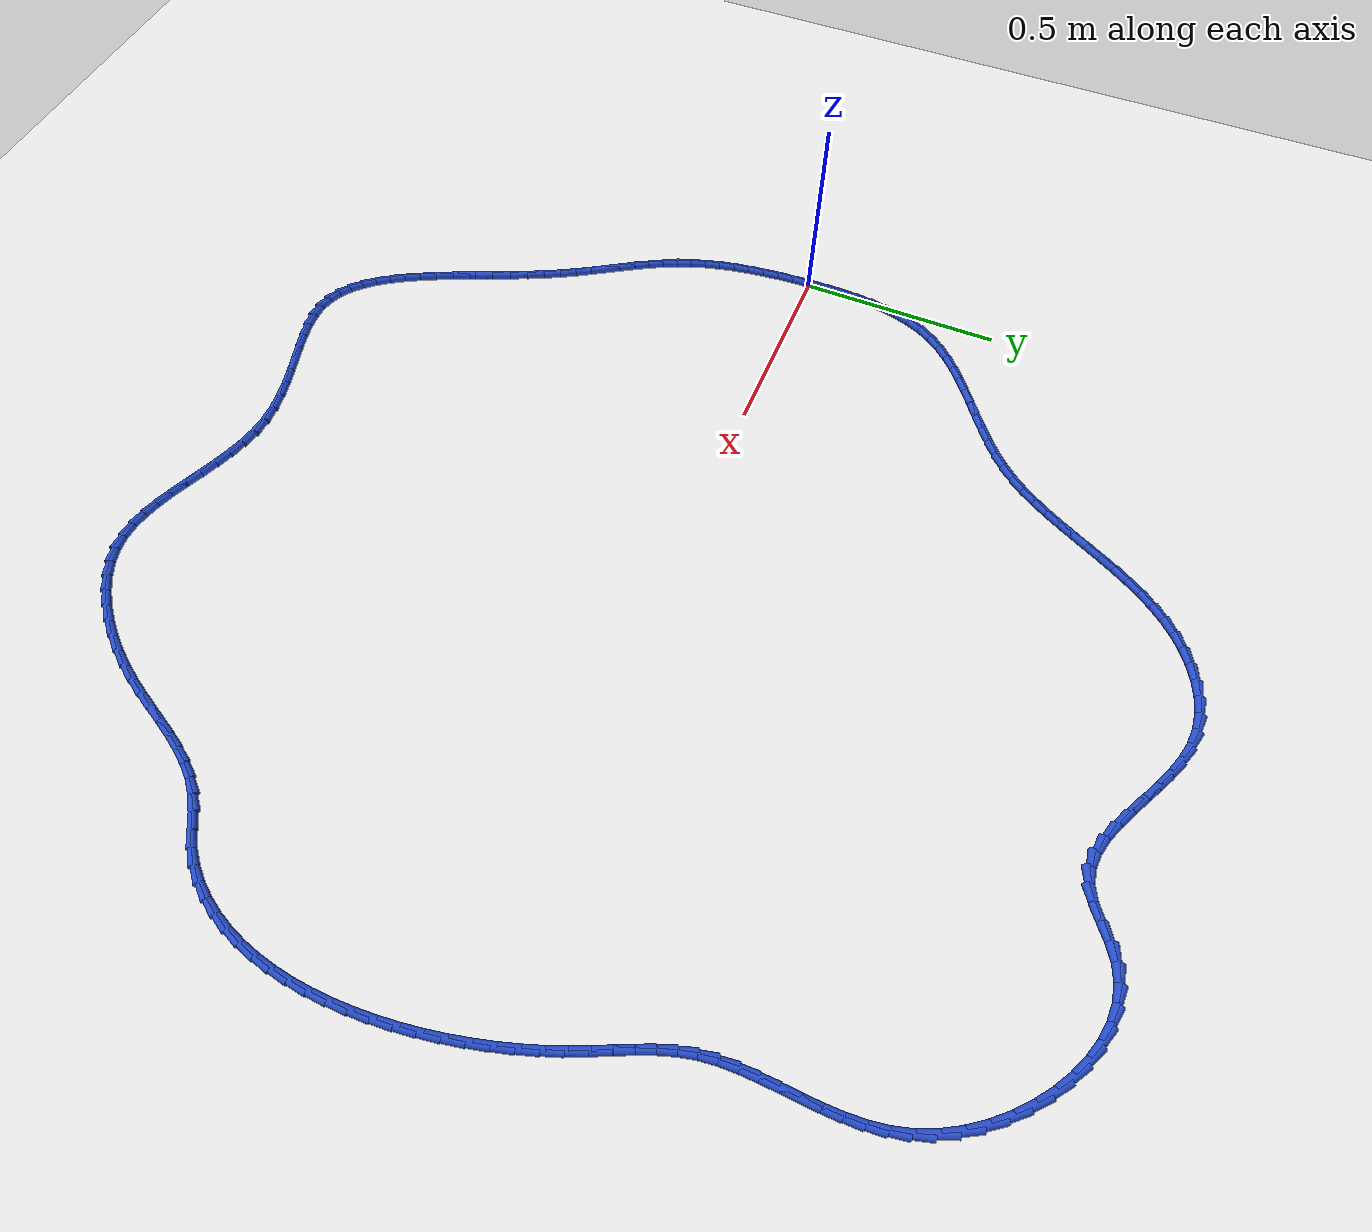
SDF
<sdf version="1.6">
 <world name="default">
  <light name="sun" type="directional">
   <pose>0 0 10 0 -0 0</pose>
   <diffuse>0.8 0.8 0.8 1</diffuse>
   <specular>0.2 0.2 0.2 1</specular>
   <attenuation>
    <range>1000</range>
    <constant>0.9</constant>
    <linear>0.01</linear>
    <quadratic>0.001</quadratic>
   </attenuation>
   <direction>-0.5 0.1 -0.9</direction>
  </light>
  <model name="ground_plane">
   <static>1</static>
   <link name="link">
    <collision name="collision">
     <geometry><plane><normal>0 0 1</normal><size>100 100</size></plane></geometry>
     <surface><friction><ode><mu>100</mu><mu2>50</mu2></ode></friction></surface>
    </collision>
    <visual name="visual">
     <cast_shadows>0</cast_shadows>
     <geometry><plane><normal>0 0 1</normal><size>100 100</size></plane></geometry>
     <material>
      <script><uri>file://media/materials/scripts/gazebo.material</uri><name>Gazebo/WhiteGlow</name></script>
     </material>
    </visual>
   </link>
  </model>
  <gravity>0 0 -9.8</gravity>
  <magnetic_field>6e-06 2.3e-05 -4.2e-05</magnetic_field>
  <atmosphere type="adiabatic"/>
  <physics name="default_physics" default="0" type="ode">
   <max_step_size>0.001</max_step_size>
   <real_time_factor>1</real_time_factor>
   <real_time_update_rate>1000</real_time_update_rate>
  </physics>
  <scene><ambient>0.4 0.4 0.4 1</ambient><background>0.7 0.7 0.7 1</background><shadows>1</shadows></scene>
  <spherical_coordinates>
   <surface_model>EARTH_WGS84</surface_model>
   <latitude_deg>0</latitude_deg>
   <longitude_deg>0</longitude_deg>
   <elevation>0</elevation>
   <heading_deg>0</heading_deg>
  </spherical_coordinates>
  <model name="line">
   <link name="link_0">
    <pose>-2.927345865710862e-17 6.938893903907228e-17 0.01 0 1.57 -1.5520164576611406</pose>
    <collision name="collision">
     <geometry><cylinder><radius>0.01</radius><length>0.08</length></cylinder></geometry>
    </collision>
    <visual name="visual">
     <material>
      <script><name>Gazebo/Blue</name><uri>file://media/materials/scripts/gazebo.material</uri></script>
     </material>
     <geometry><cylinder><radius>0.01</radius><length>0.08</length></cylinder></geometry>
    </visual>
   </link>
   <link name="link_1">
    <pose>-0.0008034517280669319 0.04277757557338744 0.01 0 1.57 1.5610438188161635</pose>
    <collision name="collision">
     <geometry><cylinder><radius>0.01</radius><length>0.08</length></cylinder></geometry>
    </collision>
    <visual name="visual">
     <material>
      <script><name>Gazebo/Blue</name><uri>file://media/materials/scripts/gazebo.material</uri></script>
     </material>
     <geometry><cylinder><radius>0.01</radius><length>0.08</length></cylinder></geometry>
    </visual>
   </link>
   <link name="link_2">
    <pose>-0.00038623956465291224 0.08555620616023513 0.01 0 1.57 1.5232267184303045</pose>
    <collision name="collision">
     <geometry><cylinder><radius>0.01</radius><length>0.08</length></cylinder></geometry>
    </collision>
    <visual name="visual">
     <material>
      <script><name>Gazebo/Blue</name><uri>file://media/materials/scripts/gazebo.material</uri></script>
     </material>
     <geometry><cylinder><radius>0.01</radius><length>0.08</length></cylinder></geometry>
    </visual>
   </link>
   <link name="link_3">
    <pose>0.001633280579723301 0.12797817854219984 0.01 0 1.57 1.475100487232595</pose>
    <collision name="collision">
     <geometry><cylinder><radius>0.01</radius><length>0.08</length></cylinder></geometry>
    </collision>
    <visual name="visual">
     <material>
      <script><name>Gazebo/Blue</name><uri>file://media/materials/scripts/gazebo.material</uri></script>
     </material>
     <geometry><cylinder><radius>0.01</radius><length>0.08</length></cylinder></geometry>
    </visual>
   </link>
   <link name="link_4">
    <pose>0.005636752794542992 0.1696857795009383 0.01 0 1.57 1.415324720007898</pose>
    <collision name="collision">
     <geometry><cylinder><radius>0.01</radius><length>0.08</length></cylinder></geometry>
    </collision>
    <visual name="visual">
     <material>
      <script><name>Gazebo/Blue</name><uri>file://media/materials/scripts/gazebo.material</uri></script>
     </material>
     <geometry><cylinder><radius>0.01</radius><length>0.08</length></cylinder></geometry>
    </visual>
   </link>
   <link name="link_5">
    <pose>0.012005821169287424 0.21032129581810716 0.01 0 1.57 1.3423311525854869</pose>
    <collision name="collision">
     <geometry><cylinder><radius>0.01</radius><length>0.08</length></cylinder></geometry>
    </collision>
    <visual name="visual">
     <material>
      <script><name>Gazebo/Blue</name><uri>file://media/materials/scripts/gazebo.material</uri></script>
     </material>
     <geometry><cylinder><radius>0.01</radius><length>0.08</length></cylinder></geometry>
    </visual>
   </link>
   <link name="link_6">
    <pose>0.02112212979343788 0.2495270142753631 0.01 0 1.57 1.2545286853556408</pose>
    <collision name="collision">
     <geometry><cylinder><radius>0.01</radius><length>0.08</length></cylinder></geometry>
    </collision>
    <visual name="visual">
     <material>
      <script><name>Gazebo/Blue</name><uri>file://media/materials/scripts/gazebo.material</uri></script>
     </material>
     <geometry><cylinder><radius>0.01</radius><length>0.08</length></cylinder></geometry>
    </visual>
   </link>
   <link name="link_7">
    <pose>0.03336732275647563 0.2869452216543629 0.01 0 1.57 1.1507070900777767</pose>
    <collision name="collision">
     <geometry><cylinder><radius>0.01</radius><length>0.08</length></cylinder></geometry>
    </collision>
    <visual name="visual">
     <material>
      <script><name>Gazebo/Blue</name><uri>file://media/materials/scripts/gazebo.material</uri></script>
     </material>
     <geometry><cylinder><radius>0.01</radius><length>0.08</length></cylinder></geometry>
    </visual>
   </link>
   <link name="link_8">
    <pose>0.049123044147881975 0.32221820473676327 0.01 0 1.57 1.0310508846193094</pose>
    <collision name="collision">
     <geometry><cylinder><radius>0.01</radius><length>0.08</length></cylinder></geometry>
    </collision>
    <visual name="visual">
     <material>
      <script><name>Gazebo/Blue</name><uri>file://media/materials/scripts/gazebo.material</uri></script>
     </material>
     <geometry><cylinder><radius>0.01</radius><length>0.08</length></cylinder></geometry>
    </visual>
   </link>
   <link name="link_9">
    <pose>0.06876020352531617 0.3549968648282729 0.01 0 1.57 0.9107668565266105</pose>
    <collision name="collision">
     <geometry><cylinder><radius>0.01</radius><length>0.08</length></cylinder></geometry>
    </collision>
    <visual name="visual">
     <material>
      <script><name>Gazebo/Blue</name><uri>file://media/materials/scripts/gazebo.material</uri></script>
     </material>
     <geometry><cylinder><radius>0.01</radius><length>0.08</length></cylinder></geometry>
    </visual>
   </link>
   <link name="link_10">
    <pose>0.0922459756503917 0.385256102750268 0.01 0 1.57 0.809878685396757</pose>
    <collision name="collision">
     <geometry><cylinder><radius>0.01</radius><length>0.08</length></cylinder></geometry>
    </collision>
    <visual name="visual">
     <material>
      <script><name>Gazebo/Blue</name><uri>file://media/materials/scripts/gazebo.material</uri></script>
     </material>
     <geometry><cylinder><radius>0.01</radius><length>0.08</length></cylinder></geometry>
    </visual>
   </link>
   <link name="link_11">
    <pose>0.11903078771923899 0.41338551224278886 0.01 0 1.57 0.7302964157931717</pose>
    <collision name="collision">
     <geometry><cylinder><radius>0.01</radius><length>0.08</length></cylinder></geometry>
    </collision>
    <visual name="visual">
     <material>
      <script><name>Gazebo/Blue</name><uri>file://media/materials/scripts/gazebo.material</uri></script>
     </material>
     <geometry><cylinder><radius>0.01</radius><length>0.08</length></cylinder></geometry>
    </visual>
   </link>
   <link name="link_12">
    <pose>0.14853129740500753 0.43980178728394675 0.01 0 1.57 0.6711364347135063</pose>
    <collision name="collision">
     <geometry><cylinder><radius>0.01</radius><length>0.08</length></cylinder></geometry>
    </collision>
    <visual name="visual">
     <material>
      <script><name>Gazebo/Blue</name><uri>file://media/materials/scripts/gazebo.material</uri></script>
     </material>
     <geometry><cylinder><radius>0.01</radius><length>0.08</length></cylinder></geometry>
    </visual>
   </link>
   <link name="link_13">
    <pose>0.18016416238084695 0.4649216218518526 0.01 0 1.57 0.630918129645902</pose>
    <collision name="collision">
     <geometry><cylinder><radius>0.01</radius><length>0.08</length></cylinder></geometry>
    </collision>
    <visual name="visual">
     <material>
      <script><name>Gazebo/Blue</name><uri>file://media/materials/scripts/gazebo.material</uri></script>
     </material>
     <geometry><cylinder><radius>0.01</radius><length>0.08</length></cylinder></geometry>
    </visual>
   </link>
   <link name="link_14">
    <pose>0.2133460403199065 0.48916170992461705 0.01 0 1.57 0.6082403466574333</pose>
    <collision name="collision">
     <geometry><cylinder><radius>0.01</radius><length>0.08</length></cylinder></geometry>
    </collision>
    <visual name="visual">
     <material>
      <script><name>Gazebo/Blue</name><uri>file://media/materials/scripts/gazebo.material</uri></script>
     </material>
     <geometry><cylinder><radius>0.01</radius><length>0.08</length></cylinder></geometry>
    </visual>
   </link>
   <link name="link_15">
    <pose>0.2474935888953359 0.5129387454803512 0.01 0 1.57 0.6021179412890646</pose>
    <collision name="collision">
     <geometry><cylinder><radius>0.01</radius><length>0.08</length></cylinder></geometry>
    </collision>
    <visual name="visual">
     <material>
      <script><name>Gazebo/Blue</name><uri>file://media/materials/scripts/gazebo.material</uri></script>
     </material>
     <geometry><cylinder><radius>0.01</radius><length>0.08</length></cylinder></geometry>
    </visual>
   </link>
   <link name="link_16">
    <pose>0.2820234657802845 0.5366694224971662 0.01 0 1.57 0.61210895259274</pose>
    <collision name="collision">
     <geometry><cylinder><radius>0.01</radius><length>0.08</length></cylinder></geometry>
    </collision>
    <visual name="visual">
     <material>
      <script><name>Gazebo/Blue</name><uri>file://media/materials/scripts/gazebo.material</uri></script>
     </material>
     <geometry><cylinder><radius>0.01</radius><length>0.08</length></cylinder></geometry>
    </visual>
   </link>
   <link name="link_17">
    <pose>0.3163523286479016 0.5607704349531727 0.01 0 1.57 0.6383233110898776</pose>
    <collision name="collision">
     <geometry><cylinder><radius>0.01</radius><length>0.08</length></cylinder></geometry>
    </collision>
    <visual name="visual">
     <material>
      <script><name>Gazebo/Blue</name><uri>file://media/materials/scripts/gazebo.material</uri></script>
     </material>
     <geometry><cylinder><radius>0.01</radius><length>0.08</length></cylinder></geometry>
    </visual>
   </link>
   <link name="link_18">
    <pose>0.3498968351713371 0.5856584768264819 0.01 0 1.57 0.6813443812744477</pose>
    <collision name="collision">
     <geometry><cylinder><radius>0.01</radius><length>0.08</length></cylinder></geometry>
    </collision>
    <visual name="visual">
     <material>
      <script><name>Gazebo/Blue</name><uri>file://media/materials/scripts/gazebo.material</uri></script>
     </material>
     <geometry><cylinder><radius>0.01</radius><length>0.08</length></cylinder></geometry>
    </visual>
   </link>
   <link name="link_19">
    <pose>0.38207364302374014 0.6117502420952047 0.01 0 1.57 0.7420412788594396</pose>
    <collision name="collision">
     <geometry><cylinder><radius>0.01</radius><length>0.08</length></cylinder></geometry>
    </collision>
    <visual name="visual">
     <material>
      <script><name>Gazebo/Blue</name><uri>file://media/materials/scripts/gazebo.material</uri></script>
     </material>
     <geometry><cylinder><radius>0.01</radius><length>0.08</length></cylinder></geometry>
    </visual>
   </link>
   <link name="link_20">
    <pose>0.4122994098782606 0.6394624247374521 0.01 0 1.57 0.8199478126077163</pose>
    <collision name="collision">
     <geometry><cylinder><radius>0.01</radius><length>0.08</length></cylinder></geometry>
    </collision>
    <visual name="visual">
     <material>
      <script><name>Gazebo/Blue</name><uri>file://media/materials/scripts/gazebo.material</uri></script>
     </material>
     <geometry><cylinder><radius>0.01</radius><length>0.08</length></cylinder></geometry>
    </visual>
   </link>
   <link name="link_21">
    <pose>0.4400318864054562 0.6691805909734477 0.01 0 1.57 0.8978571288239355</pose>
    <collision name="collision">
     <geometry><cylinder><radius>0.01</radius><length>0.08</length></cylinder></geometry>
    </collision>
    <visual name="visual">
     <material>
      <script><name>Gazebo/Blue</name><uri>file://media/materials/scripts/gazebo.material</uri></script>
     </material>
     <geometry><cylinder><radius>0.01</radius><length>0.08</length></cylinder></geometry>
    </visual>
   </link>
   <link name="link_22">
    <pose>0.4652875677167394 0.7008670606609674 0.01 0 1.57 0.9624865989774353</pose>
    <collision name="collision">
     <geometry><cylinder><radius>0.01</radius><length>0.08</length></cylinder></geometry>
    </collision>
    <visual name="visual">
     <material>
      <script><name>Gazebo/Blue</name><uri>file://media/materials/scripts/gazebo.material</uri></script>
     </material>
     <geometry><cylinder><radius>0.01</radius><length>0.08</length></cylinder></geometry>
    </visual>
   </link>
   <link name="link_23">
    <pose>0.48848605872548084 0.7341787998235954 0.01 0 1.57 1.0131785752004256</pose>
    <collision name="collision">
     <geometry><cylinder><radius>0.01</radius><length>0.08</length></cylinder></geometry>
    </collision>
    <visual name="visual">
     <material>
      <script><name>Gazebo/Blue</name><uri>file://media/materials/scripts/gazebo.material</uri></script>
     </material>
     <geometry><cylinder><radius>0.01</radius><length>0.08</length></cylinder></geometry>
    </visual>
   </link>
   <link name="link_24">
    <pose>0.51005588660736 0.7687660159119605 0.01 0 1.57 1.0500255793085147</pose>
    <collision name="collision">
     <geometry><cylinder><radius>0.01</radius><length>0.08</length></cylinder></geometry>
    </collision>
    <visual name="visual">
     <material>
      <script><name>Gazebo/Blue</name><uri>file://media/materials/scripts/gazebo.material</uri></script>
     </material>
     <geometry><cylinder><radius>0.01</radius><length>0.08</length></cylinder></geometry>
    </visual>
   </link>
   <link name="link_25">
    <pose>0.530425578538057 0.8042789163766932 0.01 0 1.57 1.073303282597267</pose>
    <collision name="collision">
     <geometry><cylinder><radius>0.01</radius><length>0.08</length></cylinder></geometry>
    </collision>
    <visual name="visual">
     <material>
      <script><name>Gazebo/Blue</name><uri>file://media/materials/scripts/gazebo.material</uri></script>
     </material>
     <geometry><cylinder><radius>0.01</radius><length>0.08</length></cylinder></geometry>
    </visual>
   </link>
   <link name="link_26">
    <pose>0.5500236616932517 0.840367708668422 0.01 0 1.57 1.0832634348189036</pose>
    <collision name="collision">
     <geometry><cylinder><radius>0.01</radius><length>0.08</length></cylinder></geometry>
    </collision>
    <visual name="visual">
     <material>
      <script><name>Gazebo/Blue</name><uri>file://media/materials/scripts/gazebo.material</uri></script>
     </material>
     <geometry><cylinder><radius>0.01</radius><length>0.08</length></cylinder></geometry>
    </visual>
   </link>
   <link name="link_27">
    <pose>0.5692786632486232 0.8766826002377766 0.01 0 1.57 1.080011696290373</pose>
    <collision name="collision">
     <geometry><cylinder><radius>0.01</radius><length>0.08</length></cylinder></geometry>
    </collision>
    <visual name="visual">
     <material>
      <script><name>Gazebo/Blue</name><uri>file://media/materials/scripts/gazebo.material</uri></script>
     </material>
     <geometry><cylinder><radius>0.01</radius><length>0.08</length></cylinder></geometry>
    </visual>
   </link>
   <link name="link_28">
    <pose>0.5886191103798518 0.9128737985353861 0.01 0 1.57 1.0634572495962729</pose>
    <collision name="collision">
     <geometry><cylinder><radius>0.01</radius><length>0.08</length></cylinder></geometry>
    </collision>
    <visual name="visual">
     <material>
      <script><name>Gazebo/Blue</name><uri>file://media/materials/scripts/gazebo.material</uri></script>
     </material>
     <geometry><cylinder><radius>0.01</radius><length>0.08</length></cylinder></geometry>
    </visual>
   </link>
   <link name="link_29">
    <pose>0.6084735302626171 0.9485915110118803 0.01 0 1.57 1.0333266390663947</pose>
    <collision name="collision">
     <geometry><cylinder><radius>0.01</radius><length>0.08</length></cylinder></geometry>
    </collision>
    <visual name="visual">
     <material>
      <script><name>Gazebo/Blue</name><uri>file://media/materials/scripts/gazebo.material</uri></script>
     </material>
     <geometry><cylinder><radius>0.01</radius><length>0.08</length></cylinder></geometry>
    </visual>
   </link>
   <link name="link_30">
    <pose>0.6292704500725986 0.9834859451178881 0.01 0 1.57 0.9892464566481233</pose>
    <collision name="collision">
     <geometry><cylinder><radius>0.01</radius><length>0.08</length></cylinder></geometry>
    </collision>
    <visual name="visual">
     <material>
      <script><name>Gazebo/Blue</name><uri>file://media/materials/scripts/gazebo.material</uri></script>
     </material>
     <geometry><cylinder><radius>0.01</radius><length>0.08</length></cylinder></geometry>
    </visual>
   </link>
   <link name="link_31">
    <pose>0.651438396985476 1.0172073083040385 0.01 0 1.57 0.9309100853064752</pose>
    <collision name="collision">
     <geometry><cylinder><radius>0.01</radius><length>0.08</length></cylinder></geometry>
    </collision>
    <visual name="visual">
     <material>
      <script><name>Gazebo/Blue</name><uri>file://media/materials/scripts/gazebo.material</uri></script>
     </material>
     <geometry><cylinder><radius>0.01</radius><length>0.08</length></cylinder></geometry>
    </visual>
   </link>
   <link name="link_32">
    <pose>0.6754058981769293 1.0494058080209618 0.01 0 1.57 0.8583427638865039</pose>
    <collision name="collision">
     <geometry><cylinder><radius>0.01</radius><length>0.08</length></cylinder></geometry>
    </collision>
    <visual name="visual">
     <material>
      <script><name>Gazebo/Blue</name><uri>file://media/materials/scripts/gazebo.material</uri></script>
     </material>
     <geometry><cylinder><radius>0.01</radius><length>0.08</length></cylinder></geometry>
    </visual>
   </link>
   <link name="link_33">
    <pose>0.7016014808226381 1.0797316517192865 0.01 0 1.57 0.772251902330791</pose>
    <collision name="collision">
     <geometry><cylinder><radius>0.01</radius><length>0.08</length></cylinder></geometry>
    </collision>
    <visual name="visual">
     <material>
      <script><name>Gazebo/Blue</name><uri>file://media/materials/scripts/gazebo.material</uri></script>
     </material>
     <geometry><cylinder><radius>0.01</radius><length>0.08</length></cylinder></geometry>
    </visual>
   </link>
   <link name="link_34">
    <pose>0.7304536720982817 1.107835046849642 0.01 0 1.57 0.674551458754761</pose>
    <collision name="collision">
     <geometry><cylinder><radius>0.01</radius><length>0.08</length></cylinder></geometry>
    </collision>
    <visual name="visual">
     <material>
      <script><name>Gazebo/Blue</name><uri>file://media/materials/scripts/gazebo.material</uri></script>
     </material>
     <geometry><cylinder><radius>0.01</radius><length>0.08</length></cylinder></geometry>
    </visual>
   </link>
   <link name="link_35">
    <pose>0.7623684716567026 1.133356970383253 0.01 0 1.57 0.5702922553740408</pose>
    <collision name="collision">
     <geometry><cylinder><radius>0.01</radius><length>0.08</length></cylinder></geometry>
    </collision>
    <visual name="visual">
     <material>
      <script><name>Gazebo/Blue</name><uri>file://media/materials/scripts/gazebo.material</uri></script>
     </material>
     <geometry><cylinder><radius>0.01</radius><length>0.08</length></cylinder></geometry>
    </visual>
   </link>
   <link name="link_36">
    <pose>0.797264849983971 1.155738842832072 0.01 0 1.57 0.4599378928380961</pose>
    <collision name="collision">
     <geometry><cylinder><radius>0.01</radius><length>0.08</length></cylinder></geometry>
    </collision>
    <visual name="visual">
     <material>
      <script><name>Gazebo/Blue</name><uri>file://media/materials/scripts/gazebo.material</uri></script>
     </material>
     <geometry><cylinder><radius>0.01</radius><length>0.08</length></cylinder></geometry>
    </visual>
   </link>
   <link name="link_37">
    <pose>0.8345914261257107 1.1742293618190092 0.01 0 1.57 0.3395098907493196</pose>
    <collision name="collision">
     <geometry><cylinder><radius>0.01</radius><length>0.08</length></cylinder></geometry>
    </collision>
    <visual name="visual">
     <material>
      <script><name>Gazebo/Blue</name><uri>file://media/materials/scripts/gazebo.material</uri></script>
     </material>
     <geometry><cylinder><radius>0.01</radius><length>0.08</length></cylinder></geometry>
    </visual>
   </link>
   <link name="link_38">
    <pose>0.8737776284195189 1.1880693617218014 0.01 0 1.57 0.20534732167251074</pose>
    <collision name="collision">
     <geometry><cylinder><radius>0.01</radius><length>0.08</length></cylinder></geometry>
    </collision>
    <visual name="visual">
     <material>
      <script><name>Gazebo/Blue</name><uri>file://media/materials/scripts/gazebo.material</uri></script>
     </material>
     <geometry><cylinder><radius>0.01</radius><length>0.08</length></cylinder></geometry>
    </visual>
   </link>
   <link name="link_39">
    <pose>0.9142528852029919 1.196499676918186 0.01 0 1.57 0.05484321418956745</pose>
    <collision name="collision">
     <geometry><cylinder><radius>0.01</radius><length>0.08</length></cylinder></geometry>
    </collision>
    <visual name="visual">
     <material>
      <script><name>Gazebo/Blue</name><uri>file://media/materials/scripts/gazebo.material</uri></script>
     </material>
     <geometry><cylinder><radius>0.01</radius><length>0.08</length></cylinder></geometry>
    </visual>
   </link>
   <link name="link_40">
    <pose>0.9554466248137254 1.198761141785898 0.01 0 1.57 -0.11114399322380754</pose>
    <collision name="collision">
     <geometry><cylinder><radius>0.01</radius><length>0.08</length></cylinder></geometry>
    </collision>
    <visual name="visual">
     <material>
      <script><name>Gazebo/Blue</name><uri>file://media/materials/scripts/gazebo.material</uri></script>
     </material>
     <geometry><cylinder><radius>0.01</radius><length>0.08</length></cylinder></geometry>
    </visual>
   </link>
   <link name="link_41">
    <pose>0.9967983997663799 1.194146121627641 0.01 0 1.57 -0.26191874773489854</pose>
    <collision name="collision">
     <geometry><cylinder><radius>0.01</radius><length>0.08</length></cylinder></geometry>
    </collision>
    <visual name="visual">
     <material>
      <script><name>Gazebo/Blue</name><uri>file://media/materials/scripts/gazebo.material</uri></script>
     </material>
     <geometry><cylinder><radius>0.01</radius><length>0.08</length></cylinder></geometry>
    </visual>
   </link>
   <link name="link_42">
    <pose>1.037975750703218 1.1831074157273853 0.01 0 1.57 -0.37001681119999813</pose>
    <collision name="collision">
     <geometry><cylinder><radius>0.01</radius><length>0.08</length></cylinder></geometry>
    </collision>
    <visual name="visual">
     <material>
      <script><name>Gazebo/Blue</name><uri>file://media/materials/scripts/gazebo.material</uri></script>
     </material>
     <geometry><cylinder><radius>0.01</radius><length>0.08</length></cylinder></geometry>
    </visual>
   </link>
   <link name="link_43">
    <pose>1.078871534331477 1.1672446568514878 0.01 0 1.57 -0.4392706588412048</pose>
    <collision name="collision">
     <geometry><cylinder><radius>0.01</radius><length>0.08</length></cylinder></geometry>
    </collision>
    <visual name="visual">
     <material>
      <script><name>Gazebo/Blue</name><uri>file://media/materials/scripts/gazebo.material</uri></script>
     </material>
     <geometry><cylinder><radius>0.01</radius><length>0.08</length></cylinder></geometry>
    </visual>
   </link>
   <link name="link_44">
    <pose>1.1193881970996455 1.148206288472975 0.01 0 1.57 -0.4744880102065574</pose>
    <collision name="collision">
     <geometry><cylinder><radius>0.01</radius><length>0.08</length></cylinder></geometry>
    </collision>
    <visual name="visual">
     <material>
      <script><name>Gazebo/Blue</name><uri>file://media/materials/scripts/gazebo.material</uri></script>
     </material>
     <geometry><cylinder><radius>0.01</radius><length>0.08</length></cylinder></geometry>
    </visual>
   </link>
   <link name="link_45">
    <pose>1.1594281854562136 1.127640754064875 0.01 0 1.57 -0.4779635355873351</pose>
    <collision name="collision">
     <geometry><cylinder><radius>0.01</radius><length>0.08</length></cylinder></geometry>
    </collision>
    <visual name="visual">
     <material>
      <script><name>Gazebo/Blue</name><uri>file://media/materials/scripts/gazebo.material</uri></script>
     </material>
     <geometry><cylinder><radius>0.01</radius><length>0.08</length></cylinder></geometry>
    </visual>
   </link>
   <link name="link_46">
    <pose>1.1988939458496706 1.1071964971002144 0.01 0 1.57 -0.4486386659905812</pose>
    <collision name="collision">
     <geometry><cylinder><radius>0.01</radius><length>0.08</length></cylinder></geometry>
    </collision>
    <visual name="visual">
     <material>
      <script><name>Gazebo/Blue</name><uri>file://media/materials/scripts/gazebo.material</uri></script>
     </material>
     <geometry><cylinder><radius>0.01</radius><length>0.08</length></cylinder></geometry>
    </visual>
   </link>
   <link name="link_47">
    <pose>1.2376879247285058 1.0885219610520214 0.01 0 1.57 -0.38156046901760965</pose>
    <collision name="collision">
     <geometry><cylinder><radius>0.01</radius><length>0.08</length></cylinder></geometry>
    </collision>
    <visual name="visual">
     <material>
      <script><name>Gazebo/Blue</name><uri>file://media/materials/scripts/gazebo.material</uri></script>
     </material>
     <geometry><cylinder><radius>0.01</radius><length>0.08</length></cylinder></geometry>
    </visual>
   </link>
   <link name="link_48">
    <pose>1.2757125685412085 1.0732655893933225 0.01 0 1.57 -0.26765002170741814</pose>
    <collision name="collision">
     <geometry><cylinder><radius>0.01</radius><length>0.08</length></cylinder></geometry>
    </collision>
    <visual name="visual">
     <material>
      <script><name>Gazebo/Blue</name><uri>file://media/materials/scripts/gazebo.material</uri></script>
     </material>
     <geometry><cylinder><radius>0.01</radius><length>0.08</length></cylinder></geometry>
    </visual>
   </link>
   <link name="link_49">
    <pose>1.3128703237362687 1.0630758255971455 0.01 0 1.57 -0.09571093538783415</pose>
    <collision name="collision">
     <geometry><cylinder><radius>0.01</radius><length>0.08</length></cylinder></geometry>
    </collision>
    <visual name="visual">
     <material>
      <script><name>Gazebo/Blue</name><uri>file://media/materials/scripts/gazebo.material</uri></script>
     </material>
     <geometry><cylinder><radius>0.01</radius><length>0.08</length></cylinder></geometry>
    </visual>
   </link>
   <link name="link_50">
    <pose>1.3490636367621747 1.0596011131365182 0.01 0 1.57 0.1382694316180792</pose>
    <collision name="collision">
     <geometry><cylinder><radius>0.01</radius><length>0.08</length></cylinder></geometry>
    </collision>
    <visual name="visual">
     <material>
      <script><name>Gazebo/Blue</name><uri>file://media/materials/scripts/gazebo.material</uri></script>
     </material>
     <geometry><cylinder><radius>0.01</radius><length>0.08</length></cylinder></geometry>
    </visual>
   </link>
   <link name="link_51">
    <pose>1.3841949540674172 1.064489895484467 0.01 0 1.57 0.40752718841273944</pose>
    <collision name="collision">
     <geometry><cylinder><radius>0.01</radius><length>0.08</length></cylinder></geometry>
    </collision>
    <visual name="visual">
     <material>
      <script><name>Gazebo/Blue</name><uri>file://media/materials/scripts/gazebo.material</uri></script>
     </material>
     <geometry><cylinder><radius>0.01</radius><length>0.08</length></cylinder></geometry>
    </visual>
   </link>
   <link name="link_52">
    <pose>1.4182029990907643 1.0791709787108392 0.01 0 1.57 0.5852635851505418</pose>
    <collision name="collision">
     <geometry><cylinder><radius>0.01</radius><length>0.08</length></cylinder></geometry>
    </collision>
    <visual name="visual">
     <material>
      <script><name>Gazebo/Blue</name><uri>file://media/materials/scripts/gazebo.material</uri></script>
     </material>
     <geometry><cylinder><radius>0.01</radius><length>0.08</length></cylinder></geometry>
    </visual>
   </link>
   <link name="link_53">
    <pose>1.4516442380203574 1.1013330732419024 0.01 0 1.57 0.6193305448351575</pose>
    <collision name="collision">
     <geometry><cylinder><radius>0.01</radius><length>0.08</length></cylinder></geometry>
    </collision>
    <visual name="visual">
     <material>
      <script><name>Gazebo/Blue</name><uri>file://media/materials/scripts/gazebo.material</uri></script>
     </material>
     <geometry><cylinder><radius>0.01</radius><length>0.08</length></cylinder></geometry>
    </visual>
   </link>
   <link name="link_54">
    <pose>1.4855921733025157 1.1255345167739434 0.01 0 1.57 0.5274261274436755</pose>
    <collision name="collision">
     <geometry><cylinder><radius>0.01</radius><length>0.08</length></cylinder></geometry>
    </collision>
    <visual name="visual">
     <material>
      <script><name>Gazebo/Blue</name><uri>file://media/materials/scripts/gazebo.material</uri></script>
     </material>
     <geometry><cylinder><radius>0.01</radius><length>0.08</length></cylinder></geometry>
    </visual>
   </link>
   <link name="link_55">
    <pose>1.5211361169980264 1.1462376103949934 0.01 0 1.57 0.32941486308088475</pose>
    <collision name="collision">
     <geometry><cylinder><radius>0.01</radius><length>0.08</length></cylinder></geometry>
    </collision>
    <visual name="visual">
     <material>
      <script><name>Gazebo/Blue</name><uri>file://media/materials/scripts/gazebo.material</uri></script>
     </material>
     <geometry><cylinder><radius>0.01</radius><length>0.08</length></cylinder></geometry>
    </visual>
   </link>
   <link name="link_56">
    <pose>1.5590030541510593 1.1591832260699642 0.01 0 1.57 0.12536663307798723</pose>
    <collision name="collision">
     <geometry><cylinder><radius>0.01</radius><length>0.08</length></cylinder></geometry>
    </collision>
    <visual name="visual">
     <material>
      <script><name>Gazebo/Blue</name><uri>file://media/materials/scripts/gazebo.material</uri></script>
     </material>
     <geometry><cylinder><radius>0.01</radius><length>0.08</length></cylinder></geometry>
    </visual>
   </link>
   <link name="link_57">
    <pose>1.5987632318542278 1.16419410487433 0.01 0 1.57 -0.05576321432500981</pose>
    <collision name="collision">
     <geometry><cylinder><radius>0.01</radius><length>0.08</length></cylinder></geometry>
    </collision>
    <visual name="visual">
     <material>
      <script><name>Gazebo/Blue</name><uri>file://media/materials/scripts/gazebo.material</uri></script>
     </material>
     <geometry><cylinder><radius>0.01</radius><length>0.08</length></cylinder></geometry>
    </visual>
   </link>
   <link name="link_58">
    <pose>1.639756555239835 1.1619058130626727 0.01 0 1.57 -0.2121239494092485</pose>
    <collision name="collision">
     <geometry><cylinder><radius>0.01</radius><length>0.08</length></cylinder></geometry>
    </collision>
    <visual name="visual">
     <material>
      <script><name>Gazebo/Blue</name><uri>file://media/materials/scripts/gazebo.material</uri></script>
     </material>
     <geometry><cylinder><radius>0.01</radius><length>0.08</length></cylinder></geometry>
    </visual>
   </link>
   <link name="link_59">
    <pose>1.681322929440184 1.1529539168895735 0.01 0 1.57 -0.3465663184024586</pose>
    <collision name="collision">
     <geometry><cylinder><radius>0.01</radius><length>0.08</length></cylinder></geometry>
    </collision>
    <visual name="visual">
     <material>
      <script><name>Gazebo/Blue</name><uri>file://media/materials/scripts/gazebo.material</uri></script>
     </material>
     <geometry><cylinder><radius>0.01</radius><length>0.08</length></cylinder></geometry>
    </visual>
   </link>
   <link name="link_60">
    <pose>1.722802259587577 1.1379739826096136 0.01 0 1.57 -0.4637715429724813</pose>
    <collision name="collision">
     <geometry><cylinder><radius>0.01</radius><length>0.08</length></cylinder></geometry>
    </collision>
    <visual name="visual">
     <material>
      <script><name>Gazebo/Blue</name><uri>file://media/materials/scripts/gazebo.material</uri></script>
     </material>
     <geometry><cylinder><radius>0.01</radius><length>0.08</length></cylinder></geometry>
    </visual>
   </link>
   <link name="link_61">
    <pose>1.7635344508143174 1.117601576477375 0.01 0 1.57 -0.5686154358692534</pose>
    <collision name="collision">
     <geometry><cylinder><radius>0.01</radius><length>0.08</length></cylinder></geometry>
    </collision>
    <visual name="visual">
     <material>
      <script><name>Gazebo/Blue</name><uri>file://media/materials/scripts/gazebo.material</uri></script>
     </material>
     <geometry><cylinder><radius>0.01</radius><length>0.08</length></cylinder></geometry>
    </visual>
   </link>
   <link name="link_62">
    <pose>1.8028594082527074 1.0924722647474387 0.01 0 1.57 -0.6655841111695917</pose>
    <collision name="collision">
     <geometry><cylinder><radius>0.01</radius><length>0.08</length></cylinder></geometry>
    </collision>
    <visual name="visual">
     <material>
      <script><name>Gazebo/Blue</name><uri>file://media/materials/scripts/gazebo.material</uri></script>
     </material>
     <geometry><cylinder><radius>0.01</radius><length>0.08</length></cylinder></geometry>
    </visual>
   </link>
   <link name="link_63">
    <pose>1.8401170370350513 1.0632216136743864 0.01 0 1.57 -0.7587377509582555</pose>
    <collision name="collision">
     <geometry><cylinder><radius>0.01</radius><length>0.08</length></cylinder></geometry>
    </collision>
    <visual name="visual">
     <material>
      <script><name>Gazebo/Blue</name><uri>file://media/materials/scripts/gazebo.material</uri></script>
     </material>
     <geometry><cylinder><radius>0.01</radius><length>0.08</length></cylinder></geometry>
    </visual>
   </link>
   <link name="link_64">
    <pose>1.87464724229365 1.0304851895127998 0.01 0 1.57 -0.8518965469132449</pose>
    <collision name="collision">
     <geometry><cylinder><radius>0.01</radius><length>0.08</length></cylinder></geometry>
    </collision>
    <visual name="visual">
     <material>
      <script><name>Gazebo/Blue</name><uri>file://media/materials/scripts/gazebo.material</uri></script>
     </material>
     <geometry><cylinder><radius>0.01</radius><length>0.08</length></cylinder></geometry>
    </visual>
   </link>
   <link name="link_65">
    <pose>1.9057899291608078 0.9948985585172601 0.01 0 1.57 -0.9488992959417957</pose>
    <collision name="collision">
     <geometry><cylinder><radius>0.01</radius><length>0.08</length></cylinder></geometry>
    </collision>
    <visual name="visual">
     <material>
      <script><name>Gazebo/Blue</name><uri>file://media/materials/scripts/gazebo.material</uri></script>
     </material>
     <geometry><cylinder><radius>0.01</radius><length>0.08</length></cylinder></geometry>
    </visual>
   </link>
   <link name="link_66">
    <pose>1.932885002768828 0.9570972869423484 0.01 0 1.57 -1.0538676209637101</pose>
    <collision name="collision">
     <geometry><cylinder><radius>0.01</radius><length>0.08</length></cylinder></geometry>
    </collision>
    <visual name="visual">
     <material>
      <script><name>Gazebo/Blue</name><uri>file://media/materials/scripts/gazebo.material</uri></script>
     </material>
     <geometry><cylinder><radius>0.01</radius><length>0.08</length></cylinder></geometry>
    </visual>
   </link>
   <link name="link_67">
    <pose>1.9552723682500122 0.9177169410426472 0.01 0 1.57 -1.1713651795048605</pose>
    <collision name="collision">
     <geometry><cylinder><radius>0.01</radius><length>0.08</length></cylinder></geometry>
    </collision>
    <visual name="visual">
     <material>
      <script><name>Gazebo/Blue</name><uri>file://media/materials/scripts/gazebo.material</uri></script>
     </material>
     <geometry><cylinder><radius>0.01</radius><length>0.08</length></cylinder></geometry>
    </visual>
   </link>
   <link name="link_68">
    <pose>1.9722942883509875 0.8773923757975108 0.01 0 1.57 -1.2965673860001043</pose>
    <collision name="collision">
     <geometry><cylinder><radius>0.01</radius><length>0.08</length></cylinder></geometry>
    </collision>
    <visual name="visual">
     <material>
      <script><name>Gazebo/Blue</name><uri>file://media/materials/scripts/gazebo.material</uri></script>
     </material>
     <geometry><cylinder><radius>0.01</radius><length>0.08</length></cylinder></geometry>
    </visual>
   </link>
   <link name="link_69">
    <pose>1.9837653652851717 0.8366159447780943 0.01 0 1.57 -1.4072158755614235</pose>
    <collision name="collision">
     <geometry><cylinder><radius>0.01</radius><length>0.08</length></cylinder></geometry>
    </collision>
    <visual name="visual">
     <material>
      <script><name>Gazebo/Blue</name><uri>file://media/materials/scripts/gazebo.material</uri></script>
     </material>
     <geometry><cylinder><radius>0.01</radius><length>0.08</length></cylinder></geometry>
    </visual>
   </link>
   <link name="link_70">
    <pose>1.9905408696688969 0.7955660394090234 0.01 0 1.57 -1.4962992142951839</pose>
    <collision name="collision">
     <geometry><cylinder><radius>0.01</radius><length>0.08</length></cylinder></geometry>
    </collision>
    <visual name="visual">
     <material>
      <script><name>Gazebo/Blue</name><uri>file://media/materials/scripts/gazebo.material</uri></script>
     </material>
     <geometry><cylinder><radius>0.01</radius><length>0.08</length></cylinder></geometry>
    </visual>
   </link>
   <link name="link_71">
    <pose>1.9936148605988815 0.7543791796320427 0.01 0 1.57 -1.5618972984908384</pose>
    <collision name="collision">
     <geometry><cylinder><radius>0.01</radius><length>0.08</length></cylinder></geometry>
    </collision>
    <visual name="visual">
     <material>
      <script><name>Gazebo/Blue</name><uri>file://media/materials/scripts/gazebo.material</uri></script>
     </material>
     <geometry><cylinder><radius>0.01</radius><length>0.08</length></cylinder></geometry>
    </visual>
   </link>
   <link name="link_72">
    <pose>1.993981397171844 0.713191885388899 0.01 0 1.57 1.5379988583110744</pose>
    <collision name="collision">
     <geometry><cylinder><radius>0.01</radius><length>0.08</length></cylinder></geometry>
    </collision>
    <visual name="visual">
     <material>
      <script><name>Gazebo/Blue</name><uri>file://media/materials/scripts/gazebo.material</uri></script>
     </material>
     <geometry><cylinder><radius>0.01</radius><length>0.08</length></cylinder></geometry>
    </visual>
   </link>
   <link name="link_73">
    <pose>1.9926345384845023 0.6721406766213368 0.01 0 1.57 1.520171018071312</pose>
    <collision name="collision">
     <geometry><cylinder><radius>0.01</radius><length>0.08</length></cylinder></geometry>
    </collision>
    <visual name="visual">
     <material>
      <script><name>Gazebo/Blue</name><uri>file://media/materials/scripts/gazebo.material</uri></script>
     </material>
     <geometry><cylinder><radius>0.01</radius><length>0.08</length></cylinder></geometry>
    </visual>
   </link>
   <link name="link_74">
    <pose>1.9905683436335748 0.6313620732711018 0.01 0 1.57 1.5264485321852774</pose>
    <collision name="collision">
     <geometry><cylinder><radius>0.01</radius><length>0.08</length></cylinder></geometry>
    </collision>
    <visual name="visual">
     <material>
      <script><name>Gazebo/Blue</name><uri>file://media/materials/scripts/gazebo.material</uri></script>
     </material>
     <geometry><cylinder><radius>0.01</radius><length>0.08</length></cylinder></geometry>
    </visual>
   </link>
   <link name="link_75">
    <pose>1.9887768717157797 0.5909925952799402 0.01 0 1.57 1.5576720280605996</pose>
    <collision name="collision">
     <geometry><cylinder><radius>0.01</radius><length>0.08</length></cylinder></geometry>
    </collision>
    <visual name="visual">
     <material>
      <script><name>Gazebo/Blue</name><uri>file://media/materials/scripts/gazebo.material</uri></script>
     </material>
     <geometry><cylinder><radius>0.01</radius><length>0.08</length></cylinder></geometry>
    </visual>
   </link>
   <link name="link_76">
    <pose>1.988254181827836 0.5511687625895975 0.01 0 1.57 -1.5263678125301645</pose>
    <collision name="collision">
     <geometry><cylinder><radius>0.01</radius><length>0.08</length></cylinder></geometry>
    </collision>
    <visual name="visual">
     <material>
      <script><name>Gazebo/Blue</name><uri>file://media/materials/scripts/gazebo.material</uri></script>
     </material>
     <geometry><cylinder><radius>0.01</radius><length>0.08</length></cylinder></geometry>
    </visual>
   </link>
   <link name="link_77">
    <pose>1.9899943330664616 0.5120270951418184 0.01 0 1.57 -1.4411348007462543</pose>
    <collision name="collision">
     <geometry><cylinder><radius>0.01</radius><length>0.08</length></cylinder></geometry>
    </collision>
    <visual name="visual">
     <material>
      <script><name>Gazebo/Blue</name><uri>file://media/materials/scripts/gazebo.material</uri></script>
     </material>
     <geometry><cylinder><radius>0.01</radius><length>0.08</length></cylinder></geometry>
    </visual>
   </link>
   <link name="link_78">
    <pose>1.9949913845283749 0.4737041128783494 0.01 0 1.57 -1.3329812186143462</pose>
    <collision name="collision">
     <geometry><cylinder><radius>0.01</radius><length>0.08</length></cylinder></geometry>
    </collision>
    <visual name="visual">
     <material>
      <script><name>Gazebo/Blue</name><uri>file://media/materials/scripts/gazebo.material</uri></script>
     </material>
     <geometry><cylinder><radius>0.01</radius><length>0.08</length></cylinder></geometry>
    </visual>
   </link>
   <link name="link_79">
    <pose>2.0040627913561546 0.4362811569882423 0.01 0 1.57 -1.2385730867904028</pose>
    <collision name="collision">
     <geometry><cylinder><radius>0.01</radius><length>0.08</length></cylinder></geometry>
    </collision>
    <visual name="visual">
     <material>
      <script><name>Gazebo/Blue</name><uri>file://media/materials/scripts/gazebo.material</uri></script>
     </material>
     <geometry><cylinder><radius>0.01</radius><length>0.08</length></cylinder></geometry>
    </visual>
   </link>
   <link name="link_80">
    <pose>2.0167708373801494 0.39944739857713935 0.01 0 1.57 -1.1745856073461858</pose>
    <collision name="collision">
     <geometry><cylinder><radius>0.01</radius><length>0.08</length></cylinder></geometry>
    </collision>
    <visual name="visual">
     <material>
      <script><name>Gazebo/Blue</name><uri>file://media/materials/scripts/gazebo.material</uri></script>
     </material>
     <geometry><cylinder><radius>0.01</radius><length>0.08</length></cylinder></geometry>
    </visual>
   </link>
   <link name="link_81">
    <pose>2.0321342368979254 0.36272217399830053 0.01 0 1.57 -1.1403210324978386</pose>
    <collision name="collision">
     <geometry><cylinder><radius>0.01</radius><length>0.08</length></cylinder></geometry>
    </collision>
    <visual name="visual">
     <material>
      <script><name>Gazebo/Blue</name><uri>file://media/materials/scripts/gazebo.material</uri></script>
     </material>
     <geometry><cylinder><radius>0.01</radius><length>0.08</length></cylinder></geometry>
    </visual>
   </link>
   <link name="link_82">
    <pose>2.049169522062165 0.3256241378080608 0.01 0 1.57 -1.1338948581145991</pose>
    <collision name="collision">
     <geometry><cylinder><radius>0.01</radius><length>0.08</length></cylinder></geometry>
    </collision>
    <visual name="visual">
     <material>
      <script><name>Gazebo/Blue</name><uri>file://media/materials/scripts/gazebo.material</uri></script>
     </material>
     <geometry><cylinder><radius>0.01</radius><length>0.08</length></cylinder></geometry>
    </visual>
   </link>
   <link name="link_83">
    <pose>2.066893225025554 0.28767194456275486 0.01 0 1.57 -1.1532536271270757</pose>
    <collision name="collision">
     <geometry><cylinder><radius>0.01</radius><length>0.08</length></cylinder></geometry>
    </collision>
    <visual name="visual">
     <material>
      <script><name>Gazebo/Blue</name><uri>file://media/materials/scripts/gazebo.material</uri></script>
     </material>
     <geometry><cylinder><radius>0.01</radius><length>0.08</length></cylinder></geometry>
    </visual>
   </link>
   <link name="link_84">
    <pose>2.0843222343114602 0.24838453971609742 0.01 0 1.57 -1.1904791453845849</pose>
    <collision name="collision">
     <geometry><cylinder><radius>0.01</radius><length>0.08</length></cylinder></geometry>
    </collision>
    <visual name="visual">
     <material>
      <script><name>Gazebo/Blue</name><uri>file://media/materials/scripts/gazebo.material</uri></script>
     </material>
     <geometry><cylinder><radius>0.01</radius><length>0.08</length></cylinder></geometry>
    </visual>
   </link>
   <link name="link_85">
    <pose>2.100685484955726 0.20745395752288748 0.01 0 1.57 -1.228871573368687</pose>
    <collision name="collision">
     <geometry><cylinder><radius>0.01</radius><length>0.08</length></cylinder></geometry>
    </collision>
    <visual name="visual">
     <material>
      <script><name>Gazebo/Blue</name><uri>file://media/materials/scripts/gazebo.material</uri></script>
     </material>
     <geometry><cylinder><radius>0.01</radius><length>0.08</length></cylinder></geometry>
    </visual>
   </link>
   <link name="link_86">
    <pose>2.1157817215130152 0.16503735493817676 0.01 0 1.57 -1.266318338247216</pose>
    <collision name="collision">
     <geometry><cylinder><radius>0.01</radius><length>0.08</length></cylinder></geometry>
    </collision>
    <visual name="visual">
     <material>
      <script><name>Gazebo/Blue</name><uri>file://media/materials/scripts/gazebo.material</uri></script>
     </material>
     <geometry><cylinder><radius>0.01</radius><length>0.08</length></cylinder></geometry>
    </visual>
   </link>
   <link name="link_87">
    <pose>2.1295044163452204 0.12136921309646838 0.01 0 1.57 -1.3033833453414247</pose>
    <collision name="collision">
     <geometry><cylinder><radius>0.01</radius><length>0.08</length></cylinder></geometry>
    </collision>
    <visual name="visual">
     <material>
      <script><name>Gazebo/Blue</name><uri>file://media/materials/scripts/gazebo.material</uri></script>
     </material>
     <geometry><cylinder><radius>0.01</radius><length>0.08</length></cylinder></geometry>
    </visual>
   </link>
   <link name="link_88">
    <pose>2.1417470418142366 0.07668401313226557 0.01 0 1.57 -1.3405867833542386</pose>
    <collision name="collision">
     <geometry><cylinder><radius>0.01</radius><length>0.08</length></cylinder></geometry>
    </collision>
    <visual name="visual">
     <material>
      <script><name>Gazebo/Blue</name><uri>file://media/materials/scripts/gazebo.material</uri></script>
     </material>
     <geometry><cylinder><radius>0.01</radius><length>0.08</length></cylinder></geometry>
    </visual>
   </link>
   <link name="link_89">
    <pose>2.1524030702819554 0.031216236180072774 0.01 0 1.57 -1.378426420192836</pose>
    <collision name="collision">
     <geometry><cylinder><radius>0.01</radius><length>0.08</length></cylinder></geometry>
    </collision>
    <visual name="visual">
     <material>
      <script><name>Gazebo/Blue</name><uri>file://media/materials/scripts/gazebo.material</uri></script>
     </material>
     <geometry><cylinder><radius>0.01</radius><length>0.08</length></cylinder></geometry>
    </visual>
   </link>
   <link name="link_90">
    <pose>2.1613659741102693 -0.014799636625606842 0.01 0 1.57 -1.4173956399340315</pose>
    <collision name="collision">
     <geometry><cylinder><radius>0.01</radius><length>0.08</length></cylinder></geometry>
    </collision>
    <visual name="visual">
     <material>
      <script><name>Gazebo/Blue</name><uri>file://media/materials/scripts/gazebo.material</uri></script>
     </material>
     <geometry><cylinder><radius>0.01</radius><length>0.08</length></cylinder></geometry>
    </visual>
   </link>
   <link name="link_91">
    <pose>2.1685292256610738 -0.06112912415026972 0.01 0 1.57 -1.4579992426390789</pose>
    <collision name="collision">
     <geometry><cylinder><radius>0.01</radius><length>0.08</length></cylinder></geometry>
    </collision>
    <visual name="visual">
     <material>
      <script><name>Gazebo/Blue</name><uri>file://media/materials/scripts/gazebo.material</uri></script>
     </material>
     <geometry><cylinder><radius>0.01</radius><length>0.08</length></cylinder></geometry>
    </visual>
   </link>
   <link name="link_92">
    <pose>2.1737862972962607 -0.10753774525941318 0.01 0 1.57 -1.5007675782116328</pose>
    <collision name="collision">
     <geometry><cylinder><radius>0.01</radius><length>0.08</length></cylinder></geometry>
    </collision>
    <visual name="visual">
     <material>
      <script><name>Gazebo/Blue</name><uri>file://media/materials/scripts/gazebo.material</uri></script>
     </material>
     <geometry><cylinder><radius>0.01</radius><length>0.08</length></cylinder></geometry>
    </visual>
   </link>
   <link name="link_93">
    <pose>2.1770306613777235 -0.1537910188185318 0.01 0 1.57 -1.546269096809606</pose>
    <collision name="collision">
     <geometry><cylinder><radius>0.01</radius><length>0.08</length></cylinder></geometry>
    </collision>
    <visual name="visual">
     <material>
      <script><name>Gazebo/Blue</name><uri>file://media/materials/scripts/gazebo.material</uri></script>
     </material>
     <geometry><cylinder><radius>0.01</radius><length>0.08</length></cylinder></geometry>
    </visual>
   </link>
   <link name="link_94">
    <pose>2.1781557902673545 -0.19965446369312276 0.01 0 1.57 1.5464718816760659</pose>
    <collision name="collision">
     <geometry><cylinder><radius>0.01</radius><length>0.08</length></cylinder></geometry>
    </collision>
    <visual name="visual">
     <material>
      <script><name>Gazebo/Blue</name><uri>file://media/materials/scripts/gazebo.material</uri></script>
     </material>
     <geometry><cylinder><radius>0.01</radius><length>0.08</length></cylinder></geometry>
    </visual>
   </link>
   <link name="link_95">
    <pose>2.1770551563270484 -0.24489359874868274 0.01 0 1.57 1.4935976904580648</pose>
    <collision name="collision">
     <geometry><cylinder><radius>0.01</radius><length>0.08</length></cylinder></geometry>
    </collision>
    <visual name="visual">
     <material>
      <script><name>Gazebo/Blue</name><uri>file://media/materials/scripts/gazebo.material</uri></script>
     </material>
     <geometry><cylinder><radius>0.01</radius><length>0.08</length></cylinder></geometry>
    </visual>
   </link>
   <link name="link_96">
    <pose>2.1736222319186966 -0.28927394285070795 0.01 0 1.57 1.4359726636568533</pose>
    <collision name="collision">
     <geometry><cylinder><radius>0.01</radius><length>0.08</length></cylinder></geometry>
    </collision>
    <visual name="visual">
     <material>
      <script><name>Gazebo/Blue</name><uri>file://media/materials/scripts/gazebo.material</uri></script>
     </material>
     <geometry><cylinder><radius>0.01</radius><length>0.08</length></cylinder></geometry>
    </visual>
   </link>
   <link name="link_97">
    <pose>2.1677504894041935 -0.3325610148646948 0.01 0 1.57 1.372822789950009</pose>
    <collision name="collision">
     <geometry><cylinder><radius>0.01</radius><length>0.08</length></cylinder></geometry>
    </collision>
    <visual name="visual">
     <material>
      <script><name>Gazebo/Blue</name><uri>file://media/materials/scripts/gazebo.material</uri></script>
     </material>
     <geometry><cylinder><radius>0.01</radius><length>0.08</length></cylinder></geometry>
    </visual>
   </link>
   <link name="link_98">
    <pose>2.159333401145432 -0.3745203336561407 0.01 0 1.57 1.3033563496669238</pose>
    <collision name="collision">
     <geometry><cylinder><radius>0.01</radius><length>0.08</length></cylinder></geometry>
    </collision>
    <visual name="visual">
     <material>
      <script><name>Gazebo/Blue</name><uri>file://media/materials/scripts/gazebo.material</uri></script>
     </material>
     <geometry><cylinder><radius>0.01</radius><length>0.08</length></cylinder></geometry>
    </visual>
   </link>
   <link name="link_99">
    <pose>2.1482644395043056 -0.41491741809054017 0.01 0 1.57 1.226818830437995</pose>
    <collision name="collision">
     <geometry><cylinder><radius>0.01</radius><length>0.08</length></cylinder></geometry>
    </collision>
    <visual name="visual">
     <material>
      <script><name>Gazebo/Blue</name><uri>file://media/materials/scripts/gazebo.material</uri></script>
     </material>
     <geometry><cylinder><radius>0.01</radius><length>0.08</length></cylinder></geometry>
    </visual>
   </link>
   <link name="link_100">
    <pose>2.1344370768427066 -0.45351778703339063 0.01 0 1.57 1.1425849199541773</pose>
    <collision name="collision">
     <geometry><cylinder><radius>0.01</radius><length>0.08</length></cylinder></geometry>
    </collision>
    <visual name="visual">
     <material>
      <script><name>Gazebo/Blue</name><uri>file://media/materials/scripts/gazebo.material</uri></script>
     </material>
     <geometry><cylinder><radius>0.01</radius><length>0.08</length></cylinder></geometry>
    </visual>
   </link>
   <link name="link_101">
    <pose>2.1177447855225293 -0.49008695935018853 0.01 0 1.57 1.050294244260722</pose>
    <collision name="collision">
     <geometry><cylinder><radius>0.01</radius><length>0.08</length></cylinder></geometry>
    </collision>
    <visual name="visual">
     <material>
      <script><name>Gazebo/Blue</name><uri>file://media/materials/scripts/gazebo.material</uri></script>
     </material>
     <geometry><cylinder><radius>0.01</radius><length>0.08</length></cylinder></geometry>
    </visual>
   </link>
   <link name="link_102">
    <pose>2.098081037905666 -0.52439045390643 0.01 0 1.57 0.9500252058325969</pose>
    <collision name="collision">
     <geometry><cylinder><radius>0.01</radius><length>0.08</length></cylinder></geometry>
    </collision>
    <visual name="visual">
     <material>
      <script><name>Gazebo/Blue</name><uri>file://media/materials/scripts/gazebo.material</uri></script>
     </material>
     <geometry><cylinder><radius>0.01</radius><length>0.08</length></cylinder></geometry>
    </visual>
   </link>
   <link name="link_103">
    <pose>2.0753393063540093 -0.5561937895676123 0.01 0 1.57 0.8424768538618533</pose>
    <collision name="collision">
     <geometry><cylinder><radius>0.01</radius><length>0.08</length></cylinder></geometry>
    </collision>
    <visual name="visual">
     <material>
      <script><name>Gazebo/Blue</name><uri>file://media/materials/scripts/gazebo.material</uri></script>
     </material>
     <geometry><cylinder><radius>0.01</radius><length>0.08</length></cylinder></geometry>
    </visual>
   </link>
   <link name="link_104">
    <pose>2.0494130632294536 -0.5852624851992305 0.01 0 1.57 0.7290968270697277</pose>
    <collision name="collision">
     <geometry><cylinder><radius>0.01</radius><length>0.08</length></cylinder></geometry>
    </collision>
    <visual name="visual">
     <material>
      <script><name>Gazebo/Blue</name><uri>file://media/materials/scripts/gazebo.material</uri></script>
     </material>
     <geometry><cylinder><radius>0.01</radius><length>0.08</length></cylinder></geometry>
    </visual>
   </link>
   <link name="link_105">
    <pose>2.0201957808938924 -0.6113620596667817 0.01 0 1.57 0.612097489538163</pose>
    <collision name="collision">
     <geometry><cylinder><radius>0.01</radius><length>0.08</length></cylinder></geometry>
    </collision>
    <visual name="visual">
     <material>
      <script><name>Gazebo/Blue</name><uri>file://media/materials/scripts/gazebo.material</uri></script>
     </material>
     <geometry><cylinder><radius>0.01</radius><length>0.08</length></cylinder></geometry>
    </visual>
   </link>
   <link name="link_106">
    <pose>1.9875816209078228 -0.634258685147866 0.01 0 1.57 0.5323627130573518</pose>
    <collision name="collision">
     <geometry><cylinder><radius>0.01</radius><length>0.08</length></cylinder></geometry>
    </collision>
    <visual name="visual">
     <material>
      <script><name>Gazebo/Blue</name><uri>file://media/materials/scripts/gazebo.material</uri></script>
     </material>
     <geometry><cylinder><radius>0.01</radius><length>0.08</length></cylinder></geometry>
    </visual>
   </link>
   <link name="link_107">
    <pose>1.952646528456824 -0.6548387820922285 0.01 0 1.57 0.5994292626092094</pose>
    <collision name="collision">
     <geometry><cylinder><radius>0.01</radius><length>0.08</length></cylinder></geometry>
    </collision>
    <visual name="visual">
     <material>
      <script><name>Gazebo/Blue</name><uri>file://media/materials/scripts/gazebo.material</uri></script>
     </material>
     <geometry><cylinder><radius>0.01</radius><length>0.08</length></cylinder></geometry>
    </visual>
   </link>
   <link name="link_108">
    <pose>1.9198755290823046 -0.6772311819813455 0.01 0 1.57 0.73868581080197</pose>
    <collision name="collision">
     <geometry><cylinder><radius>0.01</radius><length>0.08</length></cylinder></geometry>
    </collision>
    <visual name="visual">
     <material>
      <script><name>Gazebo/Blue</name><uri>file://media/materials/scripts/gazebo.material</uri></script>
     </material>
     <geometry><cylinder><radius>0.01</radius><length>0.08</length></cylinder></geometry>
    </visual>
   </link>
   <link name="link_109">
    <pose>1.891212073516334 -0.703334490752592 0.01 0 1.57 0.860132376705459</pose>
    <collision name="collision">
     <geometry><cylinder><radius>0.01</radius><length>0.08</length></cylinder></geometry>
    </collision>
    <visual name="visual">
     <material>
      <script><name>Gazebo/Blue</name><uri>file://media/materials/scripts/gazebo.material</uri></script>
     </material>
     <geometry><cylinder><radius>0.01</radius><length>0.08</length></cylinder></geometry>
    </visual>
   </link>
   <link name="link_110">
    <pose>1.8659514504195045 -0.732683972259168 0.01 0 1.57 0.9559346090463471</pose>
    <collision name="collision">
     <geometry><cylinder><radius>0.01</radius><length>0.08</length></cylinder></geometry>
    </collision>
    <visual name="visual">
     <material>
      <script><name>Gazebo/Blue</name><uri>file://media/materials/scripts/gazebo.material</uri></script>
     </material>
     <geometry><cylinder><radius>0.01</radius><length>0.08</length></cylinder></geometry>
    </visual>
   </link>
   <link name="link_111">
    <pose>1.8433106059131408 -0.7647449738555777 0.01 0 1.57 1.024781926370062</pose>
    <collision name="collision">
     <geometry><cylinder><radius>0.01</radius><length>0.08</length></cylinder></geometry>
    </collision>
    <visual name="visual">
     <material>
      <script><name>Gazebo/Blue</name><uri>file://media/materials/scripts/gazebo.material</uri></script>
     </material>
     <geometry><cylinder><radius>0.01</radius><length>0.08</length></cylinder></geometry>
    </visual>
   </link>
   <link name="link_112">
    <pose>1.8225064861185716 -0.7989828428963243 0.01 0 1.57 1.0676021989727709</pose>
    <collision name="collision">
     <geometry><cylinder><radius>0.01</radius><length>0.08</length></cylinder></geometry>
    </collision>
    <visual name="visual">
     <material>
      <script><name>Gazebo/Blue</name><uri>file://media/materials/scripts/gazebo.material</uri></script>
     </material>
     <geometry><cylinder><radius>0.01</radius><length>0.08</length></cylinder></geometry>
    </visual>
   </link>
   <link name="link_113">
    <pose>1.8027560371571232 -0.834862926735911 0.01 0 1.57 1.0860506192967376</pose>
    <collision name="collision">
     <geometry><cylinder><radius>0.01</radius><length>0.08</length></cylinder></geometry>
    </collision>
    <visual name="visual">
     <material>
      <script><name>Gazebo/Blue</name><uri>file://media/materials/scripts/gazebo.material</uri></script>
     </material>
     <geometry><cylinder><radius>0.01</radius><length>0.08</length></cylinder></geometry>
    </visual>
   </link>
   <link name="link_114">
    <pose>1.783276205150123 -0.8718505727288414 0.01 0 1.57 1.0816690452199569</pose>
    <collision name="collision">
     <geometry><cylinder><radius>0.01</radius><length>0.08</length></cylinder></geometry>
    </collision>
    <visual name="visual">
     <material>
      <script><name>Gazebo/Blue</name><uri>file://media/materials/scripts/gazebo.material</uri></script>
     </material>
     <geometry><cylinder><radius>0.01</radius><length>0.08</length></cylinder></geometry>
    </visual>
   </link>
   <link name="link_115">
    <pose>1.7632839362188963 -0.909411128229619 0.01 0 1.57 1.055614481007737</pose>
    <collision name="collision">
     <geometry><cylinder><radius>0.01</radius><length>0.08</length></cylinder></geometry>
    </collision>
    <visual name="visual">
     <material>
      <script><name>Gazebo/Blue</name><uri>file://media/materials/scripts/gazebo.material</uri></script>
     </material>
     <geometry><cylinder><radius>0.01</radius><length>0.08</length></cylinder></geometry>
    </visual>
   </link>
   <link name="link_116">
    <pose>1.7419961764847727 -0.9470099405927465 0.01 0 1.57 1.0089239515185773</pose>
    <collision name="collision">
     <geometry><cylinder><radius>0.01</radius><length>0.08</length></cylinder></geometry>
    </collision>
    <visual name="visual">
     <material>
      <script><name>Gazebo/Blue</name><uri>file://media/materials/scripts/gazebo.material</uri></script>
     </material>
     <geometry><cylinder><radius>0.01</radius><length>0.08</length></cylinder></geometry>
    </visual>
   </link>
   <link name="link_117">
    <pose>1.718638343630876 -0.9841117224363685 0.01 0 1.57 0.9495226776226715</pose>
    <collision name="collision">
     <geometry><cylinder><radius>0.01</radius><length>0.08</length></cylinder></geometry>
    </collision>
    <visual name="visual">
     <material>
      <script><name>Gazebo/Blue</name><uri>file://media/materials/scripts/gazebo.material</uri></script>
     </material>
     <geometry><cylinder><radius>0.01</radius><length>0.08</length></cylinder></geometry>
    </visual>
   </link>
   <link name="link_118">
    <pose>1.6928403037523294 -1.0201508828621473 0.01 0 1.57 0.8865395084326572</pose>
    <collision name="collision">
     <geometry><cylinder><radius>0.01</radius><length>0.08</length></cylinder></geometry>
    </collision>
    <visual name="visual">
     <material>
      <script><name>Gazebo/Blue</name><uri>file://media/materials/scripts/gazebo.material</uri></script>
     </material>
     <geometry><cylinder><radius>0.01</radius><length>0.08</length></cylinder></geometry>
    </visual>
   </link>
   <link name="link_119">
    <pose>1.6648054436129924 -1.0545188596247912 0.01 0 1.57 0.8185572634897638</pose>
    <collision name="collision">
     <geometry><cylinder><radius>0.01</radius><length>0.08</length></cylinder></geometry>
    </collision>
    <visual name="visual">
     <material>
      <script><name>Gazebo/Blue</name><uri>file://media/materials/scripts/gazebo.material</uri></script>
     </material>
     <geometry><cylinder><radius>0.01</radius><length>0.08</length></cylinder></geometry>
    </visual>
   </link>
   <link name="link_120">
    <pose>1.6347807344157417 -1.086603824891292 0.01 0 1.57 0.7431405620050722</pose>
    <collision name="collision">
     <geometry><cylinder><radius>0.01</radius><length>0.08</length></cylinder></geometry>
    </collision>
    <visual name="visual">
     <material>
      <script><name>Gazebo/Blue</name><uri>file://media/materials/scripts/gazebo.material</uri></script>
     </material>
     <geometry><cylinder><radius>0.01</radius><length>0.08</length></cylinder></geometry>
    </visual>
   </link>
   <link name="link_121">
    <pose>1.6030131473634548 -1.1157939508286399 0.01 0 1.57 0.6575092026158929</pose>
    <collision name="collision">
     <geometry><cylinder><radius>0.01</radius><length>0.08</length></cylinder></geometry>
    </collision>
    <visual name="visual">
     <material>
      <script><name>Gazebo/Blue</name><uri>file://media/materials/scripts/gazebo.material</uri></script>
     </material>
     <geometry><cylinder><radius>0.01</radius><length>0.08</length></cylinder></geometry>
    </visual>
   </link>
   <link name="link_122">
    <pose>1.5697496536590085 -1.1414774096038276 0.01 0 1.57 0.5584887843518715</pose>
    <collision name="collision">
     <geometry><cylinder><radius>0.01</radius><length>0.08</length></cylinder></geometry>
    </collision>
    <visual name="visual">
     <material>
      <script><name>Gazebo/Blue</name><uri>file://media/materials/scripts/gazebo.material</uri></script>
     </material>
     <geometry><cylinder><radius>0.01</radius><length>0.08</length></cylinder></geometry>
    </visual>
   </link>
   <link name="link_123">
    <pose>1.5352372245052794 -1.1630423733838464 0.01 0 1.57 0.4426509282426694</pose>
    <collision name="collision">
     <geometry><cylinder><radius>0.01</radius><length>0.08</length></cylinder></geometry>
    </collision>
    <visual name="visual">
     <material>
      <script><name>Gazebo/Blue</name><uri>file://media/materials/scripts/gazebo.material</uri></script>
     </material>
     <geometry><cylinder><radius>0.01</radius><length>0.08</length></cylinder></geometry>
    </visual>
   </link>
   <link name="link_124">
    <pose>1.499722831105145 -1.1798770143356878 0.01 0 1.57 0.30685634500793973</pose>
    <collision name="collision">
     <geometry><cylinder><radius>0.01</radius><length>0.08</length></cylinder></geometry>
    </collision>
    <visual name="visual">
     <material>
      <script><name>Gazebo/Blue</name><uri>file://media/materials/scripts/gazebo.material</uri></script>
     </material>
     <geometry><cylinder><radius>0.01</radius><length>0.08</length></cylinder></geometry>
    </visual>
   </link>
   <link name="link_125">
    <pose>1.4634534446614815 -1.1913695046263437 0.01 0 1.57 0.14955567193795155</pose>
    <collision name="collision">
     <geometry><cylinder><radius>0.01</radius><length>0.08</length></cylinder></geometry>
    </collision>
    <visual name="visual">
     <material>
      <script><name>Gazebo/Blue</name><uri>file://media/materials/scripts/gazebo.material</uri></script>
     </material>
     <geometry><cylinder><radius>0.01</radius><length>0.08</length></cylinder></geometry>
    </visual>
   </link>
   <link name="link_126">
    <pose>1.426675515365389 -1.1969112313760868 0.01 0 1.57 -0.01389437859304322</pose>
    <collision name="collision">
     <geometry><cylinder><radius>0.01</radius><length>0.08</length></cylinder></geometry>
    </collision>
    <visual name="visual">
     <material>
      <script><name>Gazebo/Blue</name><uri>file://media/materials/scripts/gazebo.material</uri></script>
     </material>
     <geometry><cylinder><radius>0.01</radius><length>0.08</length></cylinder></geometry>
    </visual>
   </link>
   <link name="link_127">
    <pose>1.3895541660320767 -1.1963954201010365 0.01 0 1.57 -0.1493521262012131</pose>
    <collision name="collision">
     <geometry><cylinder><radius>0.01</radius><length>0.08</length></cylinder></geometry>
    </collision>
    <visual name="visual">
     <material>
      <script><name>Gazebo/Blue</name><uri>file://media/materials/scripts/gazebo.material</uri></script>
     </material>
     <geometry><cylinder><radius>0.01</radius><length>0.08</length></cylinder></geometry>
    </visual>
   </link>
   <link name="link_128">
    <pose>1.3520856321203754 -1.190757431995173 0.01 0 1.57 -0.25081385460173256</pose>
    <collision name="collision">
     <geometry><cylinder><radius>0.01</radius><length>0.08</length></cylinder></geometry>
    </collision>
    <visual name="visual">
     <material>
      <script><name>Gazebo/Blue</name><uri>file://media/materials/scripts/gazebo.material</uri></script>
     </material>
     <geometry><cylinder><radius>0.01</radius><length>0.08</length></cylinder></geometry>
    </visual>
   </link>
   <link name="link_129">
    <pose>1.3142451260321928 -1.1810623530474171 0.01 0 1.57 -0.32036895397231685</pose>
    <collision name="collision">
     <geometry><cylinder><radius>0.01</radius><length>0.08</length></cylinder></geometry>
    </collision>
    <visual name="visual">
     <material>
      <script><name>Gazebo/Blue</name><uri>file://media/materials/scripts/gazebo.material</uri></script>
     </material>
     <geometry><cylinder><radius>0.01</radius><length>0.08</length></cylinder></geometry>
    </visual>
   </link>
   <link name="link_130">
    <pose>1.2760078601694385 -1.168375269246692 0.01 0 1.57 -0.36142019240842577</pose>
    <collision name="collision">
     <geometry><cylinder><radius>0.01</radius><length>0.08</length></cylinder></geometry>
    </collision>
    <visual name="visual">
     <material>
      <script><name>Gazebo/Blue</name><uri>file://media/materials/scripts/gazebo.material</uri></script>
     </material>
     <geometry><cylinder><radius>0.01</radius><length>0.08</length></cylinder></geometry>
    </visual>
   </link>
   <link name="link_131">
    <pose>1.2373490469340203 -1.1537612665819197 0.01 0 1.57 -0.3768366293251254</pose>
    <collision name="collision">
     <geometry><cylinder><radius>0.01</radius><length>0.08</length></cylinder></geometry>
    </collision>
    <visual name="visual">
     <material>
      <script><name>Gazebo/Blue</name><uri>file://media/materials/scripts/gazebo.material</uri></script>
     </material>
     <geometry><cylinder><radius>0.01</radius><length>0.08</length></cylinder></geometry>
    </visual>
   </link>
   <link name="link_132">
    <pose>1.1982438987278488 -1.1382854310420234 0.01 0 1.57 -0.3682946130674141</pose>
    <collision name="collision">
     <geometry><cylinder><radius>0.01</radius><length>0.08</length></cylinder></geometry>
    </collision>
    <visual name="visual">
     <material>
      <script><name>Gazebo/Blue</name><uri>file://media/materials/scripts/gazebo.material</uri></script>
     </material>
     <geometry><cylinder><radius>0.01</radius><length>0.08</length></cylinder></geometry>
    </visual>
   </link>
   <link name="link_133">
    <pose>1.158667627952833 -1.1230128486159257 0.01 0 1.57 -0.3362074346570608</pose>
    <collision name="collision">
     <geometry><cylinder><radius>0.01</radius><length>0.08</length></cylinder></geometry>
    </collision>
    <visual name="visual">
     <material>
      <script><name>Gazebo/Blue</name><uri>file://media/materials/scripts/gazebo.material</uri></script>
     </material>
     <geometry><cylinder><radius>0.01</radius><length>0.08</length></cylinder></geometry>
    </visual>
   </link>
   <link name="link_134">
    <pose>1.1185954470108808 -1.1090086052925476 0.01 0 1.57 -0.2799581414800669</pose>
    <collision name="collision">
     <geometry><cylinder><radius>0.01</radius><length>0.08</length></cylinder></geometry>
    </collision>
    <visual name="visual">
     <material>
      <script><name>Gazebo/Blue</name><uri>file://media/materials/scripts/gazebo.material</uri></script>
     </material>
     <geometry><cylinder><radius>0.01</radius><length>0.08</length></cylinder></geometry>
    </visual>
   </link>
   <link name="link_135">
    <pose>1.0780025683039018 -1.097337787060813 0.01 0 1.57 -0.19843859265833583</pose>
    <collision name="collision">
     <geometry><cylinder><radius>0.01</radius><length>0.08</length></cylinder></geometry>
    </collision>
    <visual name="visual">
     <material>
      <script><name>Gazebo/Blue</name><uri>file://media/materials/scripts/gazebo.material</uri></script>
     </material>
     <geometry><cylinder><radius>0.01</radius><length>0.08</length></cylinder></geometry>
    </visual>
   </link>
   <link name="link_136">
    <pose>1.0368642042338054 -1.0890654799096442 0.01 0 1.57 -0.09106449736590008</pose>
    <collision name="collision">
     <geometry><cylinder><radius>0.01</radius><length>0.08</length></cylinder></geometry>
    </collision>
    <visual name="visual">
     <material>
      <script><name>Gazebo/Blue</name><uri>file://media/materials/scripts/gazebo.material</uri></script>
     </material>
     <geometry><cylinder><radius>0.01</radius><length>0.08</length></cylinder></geometry>
    </visual>
   </link>
   <link name="link_137">
    <pose>0.9951555672064264 -1.085256769800181 0.01 0 1.57 0.031898642623894836</pose>
    <collision name="collision">
     <geometry><cylinder><radius>0.01</radius><length>0.08</length></cylinder></geometry>
    </collision>
    <visual name="visual">
     <material>
      <script><name>Gazebo/Blue</name><uri>file://media/materials/scripts/gazebo.material</uri></script>
     </material>
     <geometry><cylinder><radius>0.01</radius><length>0.08</length></cylinder></geometry>
    </visual>
   </link>
   <link name="link_138">
    <pose>0.9529044217797837 -1.0866049812985346 0.01 0 1.57 0.13383767226426224</pose>
    <collision name="collision">
     <geometry><cylinder><radius>0.01</radius><length>0.08</length></cylinder></geometry>
    </collision>
    <visual name="visual">
     <material>
      <script><name>Gazebo/Blue</name><uri>file://media/materials/scripts/gazebo.material</uri></script>
     </material>
     <geometry><cylinder><radius>0.01</radius><length>0.08</length></cylinder></geometry>
    </visual>
   </link>
   <link name="link_139">
    <pose>0.9103460905213547 -1.0923351441066873 0.01 0 1.57 0.20773701296250421</pose>
    <collision name="collision">
     <geometry><cylinder><radius>0.01</radius><length>0.08</length></cylinder></geometry>
    </collision>
    <visual name="visual">
     <material>
      <script><name>Gazebo/Blue</name><uri>file://media/materials/scripts/gazebo.material</uri></script>
     </material>
     <geometry><cylinder><radius>0.01</radius><length>0.08</length></cylinder></geometry>
    </visual>
   </link>
   <link name="link_140">
    <pose>0.8677671311856461 -1.101309842930285 0.01 0 1.57 0.25614774633892945</pose>
    <collision name="collision">
     <geometry><cylinder><radius>0.01</radius><length>0.08</length></cylinder></geometry>
    </collision>
    <visual name="visual">
     <material>
      <script><name>Gazebo/Blue</name><uri>file://media/materials/scripts/gazebo.material</uri></script>
     </material>
     <geometry><cylinder><radius>0.01</radius><length>0.08</length></cylinder></geometry>
    </visual>
   </link>
   <link name="link_141">
    <pose>0.8254541015271648 -1.1123916624749752 0.01 0 1.57 0.2809530001740785</pose>
    <collision name="collision">
     <geometry><cylinder><radius>0.01</radius><length>0.08</length></cylinder></geometry>
    </collision>
    <visual name="visual">
     <material>
      <script><name>Gazebo/Blue</name><uri>file://media/materials/scripts/gazebo.material</uri></script>
     </material>
     <geometry><cylinder><radius>0.01</radius><length>0.08</length></cylinder></geometry>
    </visual>
   </link>
   <link name="link_142">
    <pose>0.7836935593004178 -1.1244431874464047 0.01 0 1.57 0.28263113805526385</pose>
    <collision name="collision">
     <geometry><cylinder><radius>0.01</radius><length>0.08</length></cylinder></geometry>
    </collision>
    <visual name="visual">
     <material>
      <script><name>Gazebo/Blue</name><uri>file://media/materials/scripts/gazebo.material</uri></script>
     </material>
     <geometry><cylinder><radius>0.01</radius><length>0.08</length></cylinder></geometry>
    </visual>
   </link>
   <link name="link_143">
    <pose>0.7427720622599132 -1.1363270025502192 0.01 0 1.57 0.25981518068607434</pose>
    <collision name="collision">
     <geometry><cylinder><radius>0.01</radius><length>0.08</length></cylinder></geometry>
    </collision>
    <visual name="visual">
     <material>
      <script><name>Gazebo/Blue</name><uri>file://media/materials/scripts/gazebo.material</uri></script>
     </material>
     <geometry><cylinder><radius>0.01</radius><length>0.08</length></cylinder></geometry>
    </visual>
   </link>
   <link name="link_144">
    <pose>0.7029761681601574 -1.1469056924920662 0.01 0 1.57 0.20887697843937122</pose>
    <collision name="collision">
     <geometry><cylinder><radius>0.01</radius><length>0.08</length></cylinder></geometry>
    </collision>
    <visual name="visual">
     <material>
      <script><name>Gazebo/Blue</name><uri>file://media/materials/scripts/gazebo.material</uri></script>
     </material>
     <geometry><cylinder><radius>0.01</radius><length>0.08</length></cylinder></geometry>
    </visual>
   </link>
   <link name="link_145">
    <pose>0.6645924347556575 -1.1550418419775925 0.01 0 1.57 0.12356493972335773</pose>
    <collision name="collision">
     <geometry><cylinder><radius>0.01</radius><length>0.08</length></cylinder></geometry>
    </collision>
    <visual name="visual">
     <material>
      <script><name>Gazebo/Blue</name><uri>file://media/materials/scripts/gazebo.material</uri></script>
     </material>
     <geometry><cylinder><radius>0.01</radius><length>0.08</length></cylinder></geometry>
    </visual>
   </link>
   <link name="link_146">
    <pose>0.627907419800921 -1.1595980357124445 0.01 0 1.57 -0.004644880821836123</pose>
    <collision name="collision">
     <geometry><cylinder><radius>0.01</radius><length>0.08</length></cylinder></geometry>
    </collision>
    <visual name="visual">
     <material>
      <script><name>Gazebo/Blue</name><uri>file://media/materials/scripts/gazebo.material</uri></script>
     </material>
     <geometry><cylinder><radius>0.01</radius><length>0.08</length></cylinder></geometry>
    </visual>
   </link>
   <link name="link_147">
    <pose>0.5932076810504544 -1.159436858402269 0.01 0 1.57 -0.18252238409526975</pose>
    <collision name="collision">
     <geometry><cylinder><radius>0.01</radius><length>0.08</length></cylinder></geometry>
    </collision>
    <visual name="visual">
     <material>
      <script><name>Gazebo/Blue</name><uri>file://media/materials/scripts/gazebo.material</uri></script>
     </material>
     <geometry><cylinder><radius>0.01</radius><length>0.08</length></cylinder></geometry>
    </visual>
   </link>
   <link name="link_148">
    <pose>0.5607711666589613 -1.1534498356016099 0.01 0 1.57 -0.3831076042595102</pose>
    <collision name="collision">
     <geometry><cylinder><radius>0.01</radius><length>0.08</length></cylinder></geometry>
    </collision>
    <visual name="visual">
     <material>
      <script><name>Gazebo/Blue</name><uri>file://media/materials/scripts/gazebo.material</uri></script>
     </material>
     <geometry><cylinder><radius>0.01</radius><length>0.08</length></cylinder></geometry>
    </visual>
   </link>
   <link name="link_149">
    <pose>0.53064394570342 -1.141307945743719 0.01 0 1.57 -0.5652974676347401</pose>
    <collision name="collision">
     <geometry><cylinder><radius>0.01</radius><length>0.08</length></cylinder></geometry>
    </collision>
    <visual name="visual">
     <material>
      <script><name>Gazebo/Blue</name><uri>file://media/materials/scripts/gazebo.material</uri></script>
     </material>
     <geometry><cylinder><radius>0.01</radius><length>0.08</length></cylinder></geometry>
    </visual>
   </link>
   <link name="link_150">
    <pose>0.5026196754525605 -1.1235306401490301 0.01 0 1.57 -0.7183456507308328</pose>
    <collision name="collision">
     <geometry><cylinder><radius>0.01</radius><length>0.08</length></cylinder></geometry>
    </collision>
    <visual name="visual">
     <material>
      <script><name>Gazebo/Blue</name><uri>file://media/materials/scripts/gazebo.material</uri></script>
     </material>
     <geometry><cylinder><radius>0.01</radius><length>0.08</length></cylinder></geometry>
    </visual>
   </link>
   <link name="link_151">
    <pose>0.4764792877597872 -1.1006801461473805 0.01 0 1.57 -0.8410129608768047</pose>
    <collision name="collision">
     <geometry><cylinder><radius>0.01</radius><length>0.08</length></cylinder></geometry>
    </collision>
    <visual name="visual">
     <material>
      <script><name>Gazebo/Blue</name><uri>file://media/materials/scripts/gazebo.material</uri></script>
     </material>
     <geometry><cylinder><radius>0.01</radius><length>0.08</length></cylinder></geometry>
    </visual>
   </link>
   <link name="link_152">
    <pose>0.4520037144785048 -1.0733186910686079 0.01 0 1.57 -0.9366154658441747</pose>
    <collision name="collision">
     <geometry><cylinder><radius>0.01</radius><length>0.08</length></cylinder></geometry>
    </collision>
    <visual name="visual">
     <material>
      <script><name>Gazebo/Blue</name><uri>file://media/materials/scripts/gazebo.material</uri></script>
     </material>
     <geometry><cylinder><radius>0.01</radius><length>0.08</length></cylinder></geometry>
    </visual>
   </link>
   <link name="link_153">
    <pose>0.42897388746211723 -1.0420085022425485 0.01 0 1.57 -1.0097610591660233</pose>
    <collision name="collision">
     <geometry><cylinder><radius>0.01</radius><length>0.08</length></cylinder></geometry>
    </collision>
    <visual name="visual">
     <material>
      <script><name>Gazebo/Blue</name><uri>file://media/materials/scripts/gazebo.material</uri></script>
     </material>
     <geometry><cylinder><radius>0.01</radius><length>0.08</length></cylinder></geometry>
    </visual>
   </link>
   <link name="link_154">
    <pose>0.40717073856402836 -1.0073118069990394 0.01 0 1.57 -1.064705417962108</pose>
    <collision name="collision">
     <geometry><cylinder><radius>0.01</radius><length>0.08</length></cylinder></geometry>
    </collision>
    <visual name="visual">
     <material>
      <script><name>Gazebo/Blue</name><uri>file://media/materials/scripts/gazebo.material</uri></script>
     </material>
     <geometry><cylinder><radius>0.01</radius><length>0.08</length></cylinder></geometry>
    </visual>
   </link>
   <link name="link_155">
    <pose>0.3863751996376437 -0.9697908326679192 0.01 0 1.57 -1.1048291373343855</pose>
    <collision name="collision">
     <geometry><cylinder><radius>0.01</radius><length>0.08</length></cylinder></geometry>
    </collision>
    <visual name="visual">
     <material>
      <script><name>Gazebo/Blue</name><uri>file://media/materials/scripts/gazebo.material</uri></script>
     </material>
     <geometry><cylinder><radius>0.01</radius><length>0.08</length></cylinder></geometry>
    </visual>
   </link>
   <link name="link_156">
    <pose>0.36636820253636676 -0.9300078065790242 0.01 0 1.57 -1.1326092457012205</pose>
    <collision name="collision">
     <geometry><cylinder><radius>0.01</radius><length>0.08</length></cylinder></geometry>
    </collision>
    <visual name="visual">
     <material>
      <script><name>Gazebo/Blue</name><uri>file://media/materials/scripts/gazebo.material</uri></script>
     </material>
     <geometry><cylinder><radius>0.01</radius><length>0.08</length></cylinder></geometry>
    </visual>
   </link>
   <link name="link_157">
    <pose>0.3469306791136022 -0.8885249560621915 0.01 0 1.57 -1.149740566348047</pose>
    <collision name="collision">
     <geometry><cylinder><radius>0.01</radius><length>0.08</length></cylinder></geometry>
    </collision>
    <visual name="visual">
     <material>
      <script><name>Gazebo/Blue</name><uri>file://media/materials/scripts/gazebo.material</uri></script>
     </material>
     <geometry><cylinder><radius>0.01</radius><length>0.08</length></cylinder></geometry>
    </visual>
   </link>
   <link name="link_158">
    <pose>0.32784356122275404 -0.8459045084472586 0.01 0 1.57 -1.1572669975052021</pose>
    <collision name="collision">
     <geometry><cylinder><radius>0.01</radius><length>0.08</length></cylinder></geometry>
    </collision>
    <visual name="visual">
     <material>
      <script><name>Gazebo/Blue</name><uri>file://media/materials/scripts/gazebo.material</uri></script>
     </material>
     <geometry><cylinder><radius>0.01</radius><length>0.08</length></cylinder></geometry>
    </visual>
   </link>
   <link name="link_159">
    <pose>0.3088877807172264 -0.8027086910640616 0.01 0 1.57 -1.155677509951657</pose>
    <collision name="collision">
     <geometry><cylinder><radius>0.01</radius><length>0.08</length></cylinder></geometry>
    </collision>
    <visual name="visual">
     <material>
      <script><name>Gazebo/Blue</name><uri>file://media/materials/scripts/gazebo.material</uri></script>
     </material>
     <geometry><cylinder><radius>0.01</radius><length>0.08</length></cylinder></geometry>
    </visual>
   </link>
   <link name="link_160">
    <pose>0.28984426945042413 -0.7594997312424392 0.01 0 1.57 -1.1449567393576783</pose>
    <collision name="collision">
     <geometry><cylinder><radius>0.01</radius><length>0.08</length></cylinder></geometry>
    </collision>
    <visual name="visual">
     <material>
      <script><name>Gazebo/Blue</name><uri>file://media/materials/scripts/gazebo.material</uri></script>
     </material>
     <geometry><cylinder><radius>0.01</radius><length>0.08</length></cylinder></geometry>
    </visual>
   </link>
   <link name="link_161">
    <pose>0.27049395927575137 -0.7168398563122284 0.01 0 1.57 -1.1245903852774177</pose>
    <collision name="collision">
     <geometry><cylinder><radius>0.01</radius><length>0.08</length></cylinder></geometry>
    </collision>
    <visual name="visual">
     <material>
      <script><name>Gazebo/Blue</name><uri>file://media/materials/scripts/gazebo.material</uri></script>
     </material>
     <geometry><cylinder><radius>0.01</radius><length>0.08</length></cylinder></geometry>
    </visual>
   </link>
   <link name="link_162">
    <pose>0.25061778204661234 -0.6752912936032656 0.01 0 1.57 -1.0935523205934499</pose>
    <collision name="collision">
     <geometry><cylinder><radius>0.01</radius><length>0.08</length></cylinder></geometry>
    </collision>
    <visual name="visual">
     <material>
      <script><name>Gazebo/Blue</name><uri>file://media/materials/scripts/gazebo.material</uri></script>
     </material>
     <geometry><cylinder><radius>0.01</radius><length>0.08</length></cylinder></geometry>
    </visual>
   </link>
   <link name="link_163">
    <pose>0.2299973380813779 -0.6354151960422405 0.01 0 1.57 -1.0564803110231522</pose>
    <collision name="collision">
     <geometry><cylinder><radius>0.01</radius><length>0.08</length></cylinder></geometry>
    </collision>
    <visual name="visual">
     <material>
      <script><name>Gazebo/Blue</name><uri>file://media/materials/scripts/gazebo.material</uri></script>
     </material>
     <geometry><cylinder><radius>0.01</radius><length>0.08</length></cylinder></geometry>
    </visual>
   </link>
   <link name="link_164">
    <pose>0.20857859766779266 -0.597508529767604 0.01 0 1.57 -1.027474606590848</pose>
    <collision name="collision">
     <geometry><cylinder><radius>0.01</radius><length>0.08</length></cylinder></geometry>
    </collision>
    <visual name="visual">
     <material>
      <script><name>Gazebo/Blue</name><uri>file://media/materials/scripts/gazebo.material</uri></script>
     </material>
     <geometry><cylinder><radius>0.01</radius><length>0.08</length></cylinder></geometry>
    </visual>
   </link>
   <link name="link_165">
    <pose>0.18668606684531697 -0.5612598520651431 0.01 0 1.57 -1.0097028255412965</pose>
    <collision name="collision">
     <geometry><cylinder><radius>0.01</radius><length>0.08</length></cylinder></geometry>
    </collision>
    <visual name="visual">
     <material>
      <script><name>Gazebo/Blue</name><uri>file://media/materials/scripts/gazebo.material</uri></script>
     </material>
     <geometry><cylinder><radius>0.01</radius><length>0.08</length></cylinder></geometry>
    </visual>
   </link>
   <link name="link_166">
    <pose>0.1646973509317662 -0.5262723753863107 0.01 0 1.57 -1.004221080705151</pose>
    <collision name="collision">
     <geometry><cylinder><radius>0.01</radius><length>0.08</length></cylinder></geometry>
    </collision>
    <visual name="visual">
     <material>
      <script><name>Gazebo/Blue</name><uri>file://media/materials/scripts/gazebo.material</uri></script>
     </material>
     <geometry><cylinder><radius>0.01</radius><length>0.08</length></cylinder></geometry>
    </visual>
   </link>
   <link name="link_167">
    <pose>0.14299005524495464 -0.4921493121825575 0.01 0 1.57 -1.01190601236502</pose>
    <collision name="collision">
     <geometry><cylinder><radius>0.01</radius><length>0.08</length></cylinder></geometry>
    </collision>
    <visual name="visual">
     <material>
      <script><name>Gazebo/Blue</name><uri>file://media/materials/scripts/gazebo.material</uri></script>
     </material>
     <geometry><cylinder><radius>0.01</radius><length>0.08</length></cylinder></geometry>
    </visual>
   </link>
   <link name="link_168">
    <pose>0.12194178510269663 -0.4584938749053352 0.01 0 1.57 -1.0334282588355437</pose>
    <collision name="collision">
     <geometry><cylinder><radius>0.01</radius><length>0.08</length></cylinder></geometry>
    </collision>
    <visual name="visual">
     <material>
      <script><name>Gazebo/Blue</name><uri>file://media/materials/scripts/gazebo.material</uri></script>
     </material>
     <geometry><cylinder><radius>0.01</radius><length>0.08</length></cylinder></geometry>
    </visual>
   </link>
   <link name="link_169">
    <pose>0.10193014582280685 -0.42490927600609535 0.01 0 1.57 -1.0691628888056066</pose>
    <collision name="collision">
     <geometry><cylinder><radius>0.01</radius><length>0.08</length></cylinder></geometry>
    </collision>
    <visual name="visual">
     <material>
      <script><name>Gazebo/Blue</name><uri>file://media/materials/scripts/gazebo.material</uri></script>
     </material>
     <geometry><cylinder><radius>0.01</radius><length>0.08</length></cylinder></geometry>
    </visual>
   </link>
   <link name="link_170">
    <pose>0.08333274272309944 -0.390998727936289 0.01 0 1.57 -1.1190237988855816</pose>
    <collision name="collision">
     <geometry><cylinder><radius>0.01</radius><length>0.08</length></cylinder></geometry>
    </collision>
    <visual name="visual">
     <material>
      <script><name>Gazebo/Blue</name><uri>file://media/materials/scripts/gazebo.material</uri></script>
     </material>
     <geometry><cylinder><radius>0.01</radius><length>0.08</length></cylinder></geometry>
    </visual>
   </link>
   <link name="link_171">
    <pose>0.06652718112138964 -0.35636544314736857 0.01 0 1.57 -1.1816044693950196</pose>
    <collision name="collision">
     <geometry><cylinder><radius>0.01</radius><length>0.08</length></cylinder></geometry>
    </collision>
    <visual name="visual">
     <material>
      <script><name>Gazebo/Blue</name><uri>file://media/materials/scripts/gazebo.material</uri></script>
     </material>
     <geometry><cylinder><radius>0.01</radius><length>0.08</length></cylinder></geometry>
    </visual>
   </link>
   <link name="link_172">
    <pose>0.05187181114306596 -0.3206302726393776 0.01 0 1.57 -1.2459785659410767</pose>
    <collision name="collision">
     <geometry><cylinder><radius>0.01</radius><length>0.08</length></cylinder></geometry>
    </collision>
    <visual name="visual">
     <material>
      <script><name>Gazebo/Blue</name><uri>file://media/materials/scripts/gazebo.material</uri></script>
     </material>
     <geometry><cylinder><radius>0.01</radius><length>0.08</length></cylinder></geometry>
    </visual>
   </link>
   <link name="link_173">
    <pose>0.03943033635263769 -0.2836839757865124 0.01 0 1.57 -1.3041717452987966</pose>
    <collision name="collision">
     <geometry><cylinder><radius>0.01</radius><length>0.08</length></cylinder></geometry>
    </collision>
    <visual name="visual">
     <material>
      <script><name>Gazebo/Blue</name><uri>file://media/materials/scripts/gazebo.material</uri></script>
     </material>
     <geometry><cylinder><radius>0.01</radius><length>0.08</length></cylinder></geometry>
    </visual>
   </link>
   <link name="link_174">
    <pose>0.02903625300042758 -0.24562819133554586 0.01 0 1.57 -1.3560404322056192</pose>
    <collision name="collision">
     <geometry><cylinder><radius>0.01</radius><length>0.08</length></cylinder></geometry>
    </collision>
    <visual name="visual">
     <material>
      <script><name>Gazebo/Blue</name><uri>file://media/materials/scripts/gazebo.material</uri></script>
     </material>
     <geometry><cylinder><radius>0.01</radius><length>0.08</length></cylinder></geometry>
    </visual>
   </link>
   <link name="link_175">
    <pose>0.02051693656697583 -0.20657016491023483 0.01 0 1.57 -1.40179417815137</pose>
    <collision name="collision">
     <geometry><cylinder><radius>0.01</radius><length>0.08</length></cylinder></geometry>
    </collision>
    <visual name="visual">
     <material>
      <script><name>Gazebo/Blue</name><uri>file://media/materials/scripts/gazebo.material</uri></script>
     </material>
     <geometry><cylinder><radius>0.01</radius><length>0.08</length></cylinder></geometry>
    </visual>
   </link>
   <link name="link_176">
    <pose>0.01369976253282253 -0.1666171421343353 0.01 0 1.57 -1.4417299827277483</pose>
    <collision name="collision">
     <geometry><cylinder><radius>0.01</radius><length>0.08</length></cylinder></geometry>
    </collision>
    <visual name="visual">
     <material>
      <script><name>Gazebo/Blue</name><uri>file://media/materials/scripts/gazebo.material</uri></script>
     </material>
     <geometry><cylinder><radius>0.01</radius><length>0.08</length></cylinder></geometry>
    </visual>
   </link>
   <link name="link_177">
    <pose>0.00841210637850817 -0.12587636863160567 0.01 0 1.57 -1.476182475867089</pose>
    <collision name="collision">
     <geometry><cylinder><radius>0.01</radius><length>0.08</length></cylinder></geometry>
    </collision>
    <visual name="visual">
     <material>
      <script><name>Gazebo/Blue</name><uri>file://media/materials/scripts/gazebo.material</uri></script>
     </material>
     <geometry><cylinder><radius>0.01</radius><length>0.08</length></cylinder></geometry>
    </visual>
   </link>
   <link name="link_178">
    <pose>0.004481343584572816 -0.084455090025802 0.01 0 1.57 -1.5054881172062957</pose>
    <collision name="collision">
     <geometry><cylinder><radius>0.01</radius><length>0.08</length></cylinder></geometry>
    </collision>
    <visual name="visual">
     <material>
      <script><name>Gazebo/Blue</name><uri>file://media/materials/scripts/gazebo.material</uri></script>
     </material>
     <geometry><cylinder><radius>0.01</radius><length>0.08</length></cylinder></geometry>
    </visual>
   </link>
   <link name="link_179">
    <pose>0.0017348496315566723 -0.042460551940681046 0.01 0 1.57 -1.5299611244744107</pose>
    <collision name="collision">
     <geometry><cylinder><radius>0.01</radius><length>0.08</length></cylinder></geometry>
    </collision>
    <visual name="visual">
     <material>
      <script><name>Gazebo/Blue</name><uri>file://media/materials/scripts/gazebo.material</uri></script>
     </material>
     <geometry><cylinder><radius>0.01</radius><length>0.08</length></cylinder></geometry>
    </visual>
   </link>
   <link name="link_180">
    <pose>-4.185020385794047e-17 2.636779683484747e-16 0.01 0 1.57 -1.5498782187957985</pose>
    <collision name="collision">
     <geometry><cylinder><radius>0.01</radius><length>0.08</length></cylinder></geometry>
    </collision>
    <visual name="visual">
     <material>
      <script><name>Gazebo/Blue</name><uri>file://media/materials/scripts/gazebo.material</uri></script>
     </material>
     <geometry><cylinder><radius>0.01</radius><length>0.08</length></cylinder></geometry>
    </visual>
   </link>
   <link name="link_181">
    <pose>-0.0008958298295571165 0.042819320172485284 0.01 0 1.57 -1.5498782187957982</pose>
    <collision name="collision">
     <geometry><cylinder><radius>0.01</radius><length>0.08</length></cylinder></geometry>
    </collision>
    <visual name="visual">
     <material>
      <script><name>Gazebo/Blue</name><uri>file://media/materials/scripts/gazebo.material</uri></script>
     </material>
     <geometry><cylinder><radius>0.01</radius><length>0.08</length></cylinder></geometry>
    </visual>
   </link>
  </model>
 </world>
</sdf>
